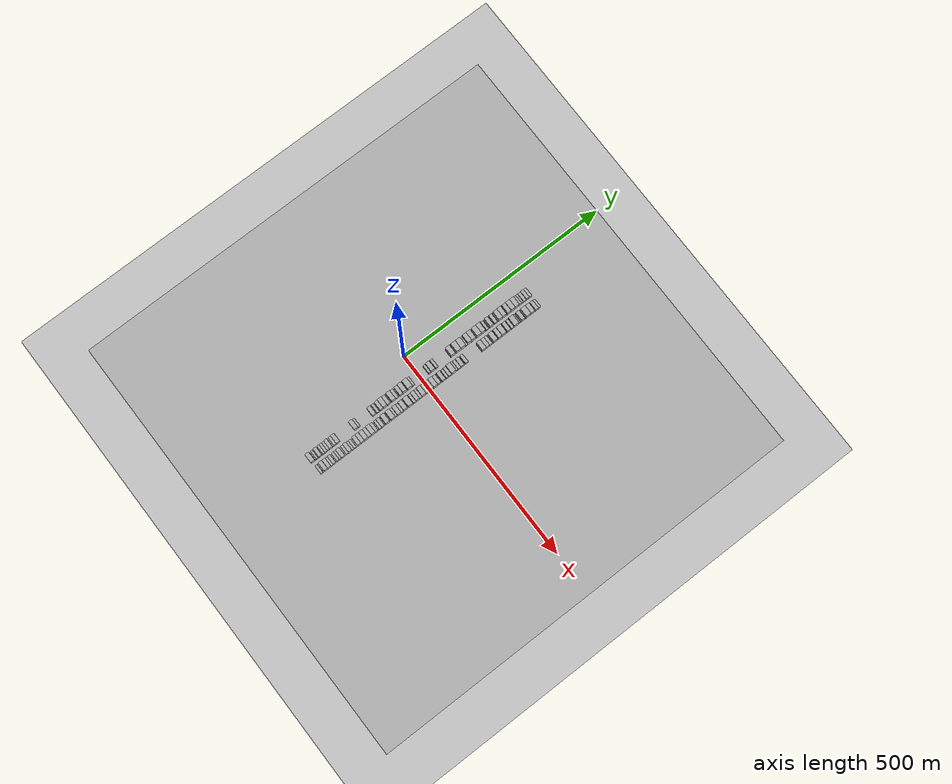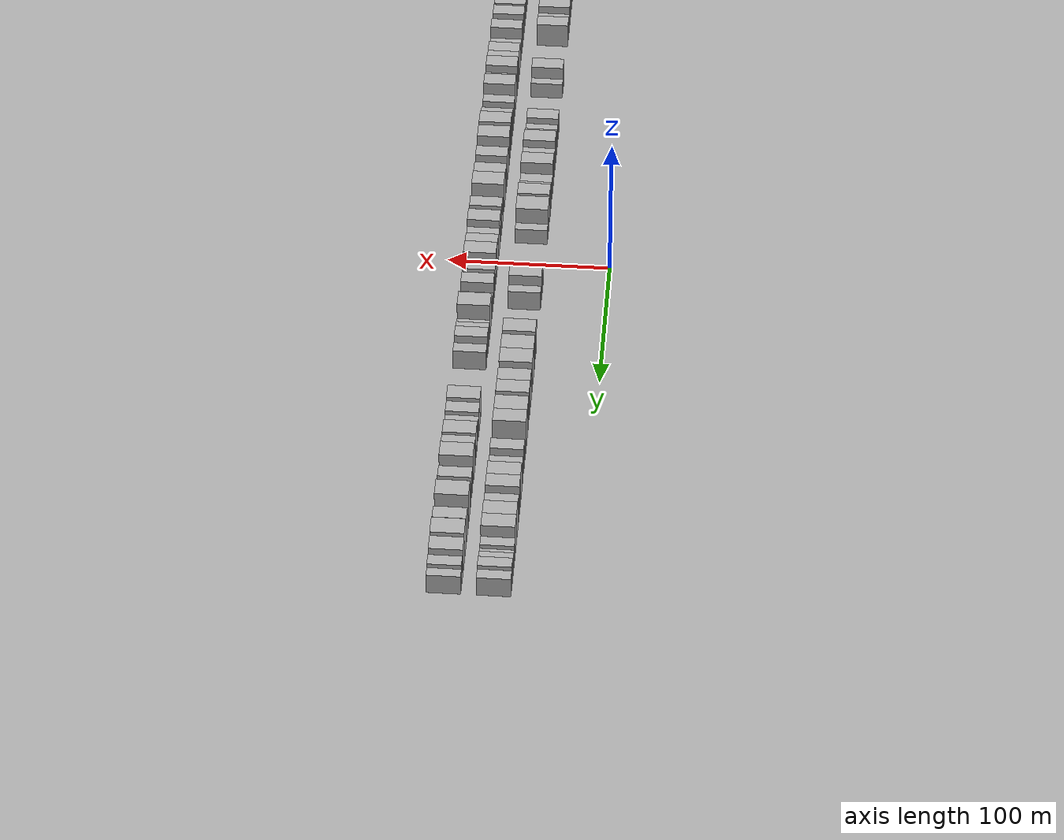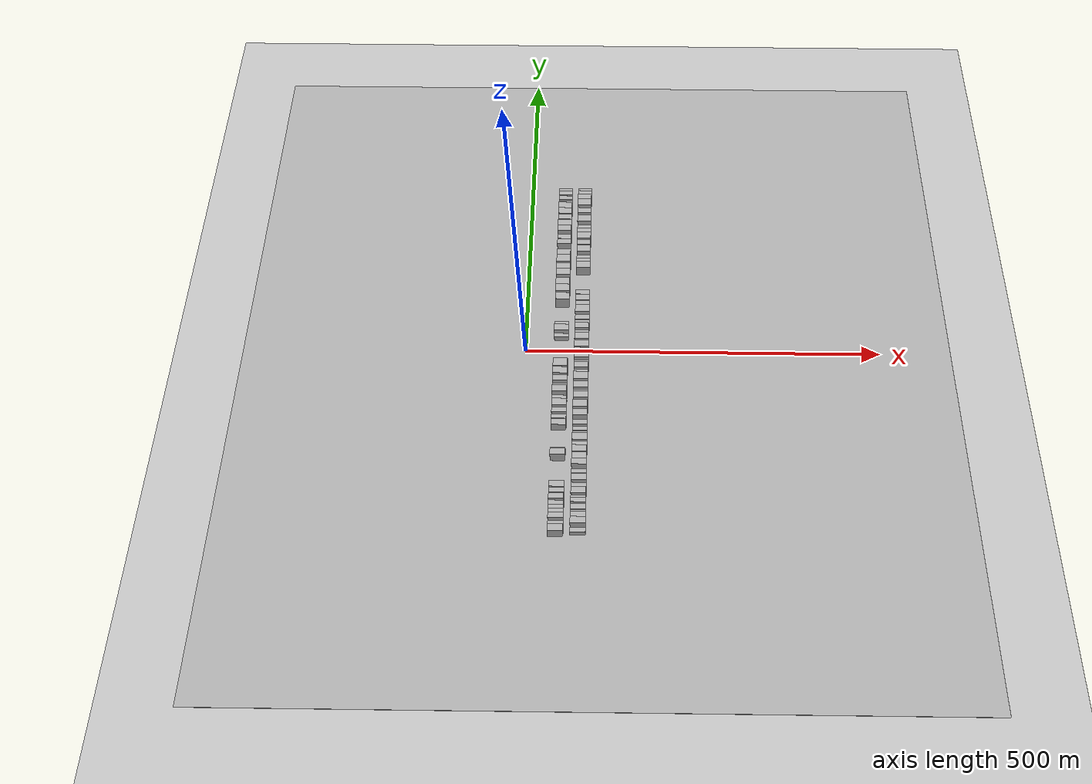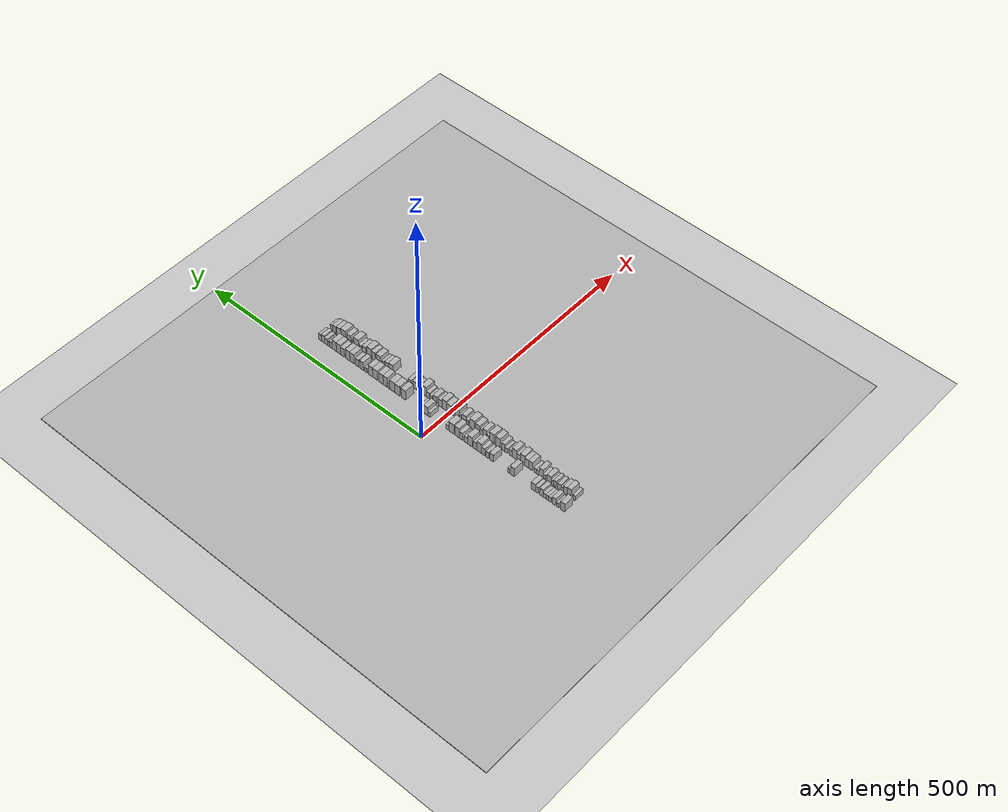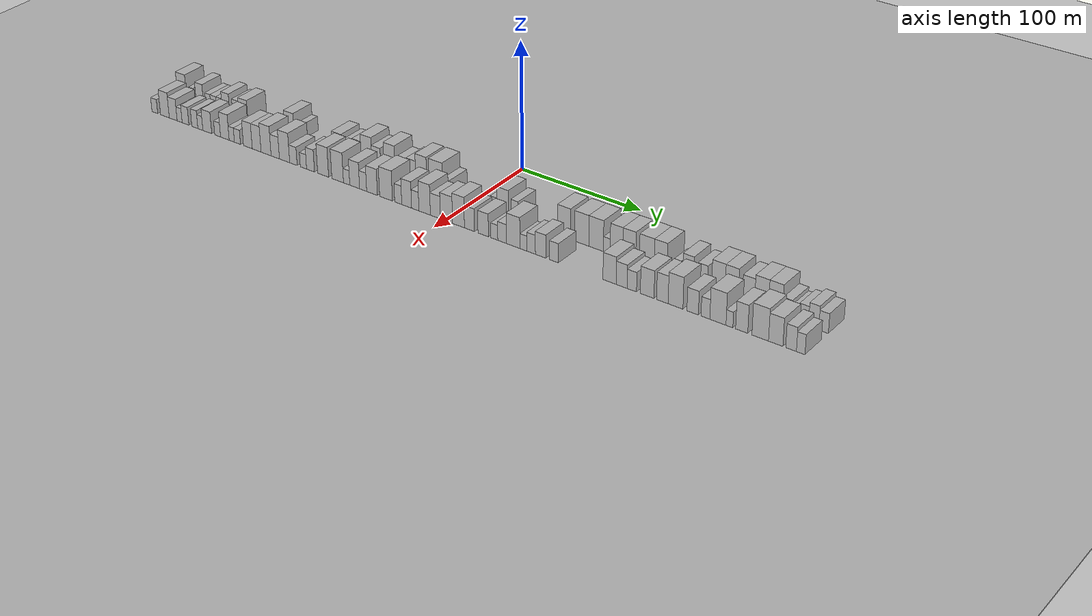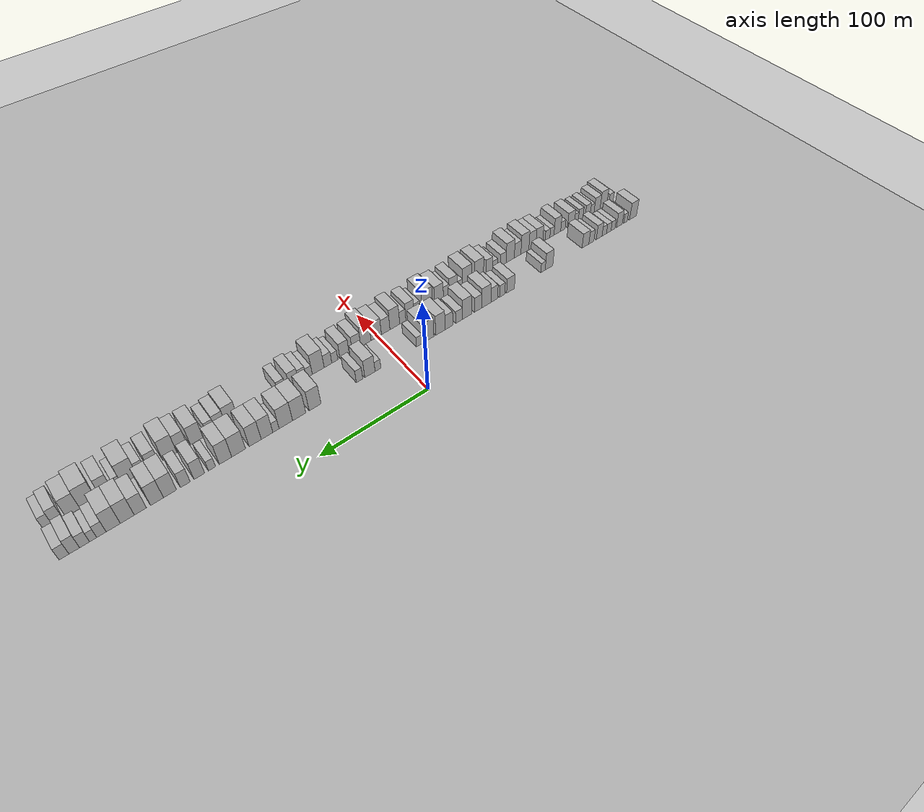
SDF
<?xml version="1.0" encoding="utf-8"?>

<sdf version="1.6">

   <world name="default">

      <gui fullscreen="0">

         <camera name="user_camera">

            <pose>-15 0 4.57585 0 0 0</pose>

            <view_controller>orbit</view_controller>

         </camera>

      </gui>

      <scene>

         <sky>

           <clouds>

             <speed>12</speed>

           </clouds>

         </sky>

         <ambient>0.4 0.4 0.4 1</ambient>

         <background>0.7 0.7 0.7 1</background>

         <shadows>1</shadows>

      </scene>

      <gravity>0 0 -9.8066</gravity>

      <magnetic_field>6e-06 2.3e-05 -4.2e-05</magnetic_field>

      <physics default="0" name="default_physics" type="ode">

         <ode>

            <solver>

               <type>quick</type>

               <iters>10</iters>

               <sor>1.0</sor>

               <use_dynamic_moi_rescaling>0</use_dynamic_moi_rescaling>

            </solver>

            <constraints>

               <cfm>0</cfm>

               <erp>0.2</erp>

               <contact_max_correcting_vel>100</contact_max_correcting_vel>

               <contact_surface_layer>0.001</contact_surface_layer>

            </constraints>

         </ode>

         <max_step_size>0.004</max_step_size>

         <real_time_factor>1</real_time_factor>

         <real_time_update_rate>250</real_time_update_rate>

      </physics>

      <light name="sun" type="directional">

         <cast_shadows>1</cast_shadows>

         <pose>0 0 10 0 0 0</pose>

         <diffuse>0.8 0.8 0.8 1</diffuse>

         <specular>0.2 0.2 0.2 1</specular>

         <attenuation>

            <range>1000</range>

            <constant>0.9</constant>

            <linear>0.01</linear>

            <quadratic>0.001</quadratic>

         </attenuation>

         <direction>-0.5 0.1 -0.9</direction>

      </light>

      <include>

         <name>ground_plane_1</name>

         <uri>model://HANNAS_ground_plane</uri>

         <pose>0 0 0  0 0 0</pose>

      </include>

      <include>

         <name>ground_plane_2</name>

         <uri>model://HANNAS_ground_plane</uri>

         <pose>100 0 0  0 0 0</pose>

      </include>

      <model name="building_1">

         <static>1</static>

         <pose frame="">50.0000 -273.2894 0 0.000000 0.000000 0.000000</pose>

         <link name="link">

            <pose frame="">0 0 10.50 0 0 0</pose>

            <collision name="collision">

               <geometry>

                  <box>

                     <size>20.0000 9.4211 21.0000</size>

                  </box>

               </geometry>

               <max_contacts>10</max_contacts>

               <surface>

                  <contact>

                     <ode/>

                  </contact>

                  <bounce/>

                  <friction>

                     <torsional>

                        <ode/>

                     </torsional>

                     <ode/>

                  </friction>

               </surface>

            </collision>

            <visual name="visual">

               <cast_shadows>0</cast_shadows>

               <geometry>

                  <box>

                     <size>20.0000 9.4211 21.0000</size>

                  </box>

               </geometry>

               <material>

                  <script>

                     <uri>model://HANNAS_wall/materials/scripts</uri>

                     <uri>model://HANNAS_wall/materials/textures</uri>

                     <name>vrc/HANNAS_wall</name>

                  </script>

               </material>

            </visual>

            <self_collide>0</self_collide>

            <enable_wind>0</enable_wind>

            <kinematic>0</kinematic>

         </link>

      </model>

      <model name="building_2">

         <static>1</static>

         <pose frame="">50.0000 -263.1731 0 0.000000 0.000000 0.000000</pose>

         <link name="link">

            <pose frame="">0 0 6.00 0 0 0</pose>

            <collision name="collision">

               <geometry>

                  <box>

                     <size>20.0000 4.8114 12.0000</size>

                  </box>

               </geometry>

               <max_contacts>10</max_contacts>

               <surface>

                  <contact>

                     <ode/>

                  </contact>

                  <bounce/>

                  <friction>

                     <torsional>

                        <ode/>

                     </torsional>

                     <ode/>

                  </friction>

               </surface>

            </collision>

            <visual name="visual">

               <cast_shadows>0</cast_shadows>

               <geometry>

                  <box>

                     <size>20.0000 4.8114 12.0000</size>

                  </box>

               </geometry>

               <material>

                  <script>

                     <uri>model://HANNAS_wall/materials/scripts</uri>

                     <uri>model://HANNAS_wall/materials/textures</uri>

                     <name>vrc/HANNAS_wall</name>

                  </script>

               </material>

            </visual>

            <self_collide>0</self_collide>

            <enable_wind>0</enable_wind>

            <kinematic>0</kinematic>

         </link>

      </model>

      <model name="building_3">

         <static>1</static>

         <pose frame="">50.0000 -254.9956 0 0.000000 0.000000 0.000000</pose>

         <link name="link">

            <pose frame="">0 0 9.00 0 0 0</pose>

            <collision name="collision">

               <geometry>

                  <box>

                     <size>20.0000 7.5438 18.0000</size>

                  </box>

               </geometry>

               <max_contacts>10</max_contacts>

               <surface>

                  <contact>

                     <ode/>

                  </contact>

                  <bounce/>

                  <friction>

                     <torsional>

                        <ode/>

                     </torsional>

                     <ode/>

                  </friction>

               </surface>

            </collision>

            <visual name="visual">

               <cast_shadows>0</cast_shadows>

               <geometry>

                  <box>

                     <size>20.0000 7.5438 18.0000</size>

                  </box>

               </geometry>

               <material>

                  <script>

                     <uri>model://HANNAS_wall/materials/scripts</uri>

                     <uri>model://HANNAS_wall/materials/textures</uri>

                     <name>vrc/HANNAS_wall</name>

                  </script>

               </material>

            </visual>

            <self_collide>0</self_collide>

            <enable_wind>0</enable_wind>

            <kinematic>0</kinematic>

         </link>

      </model>

      <model name="building_4">

         <static>1</static>

         <pose frame="">50.0000 -246.5318 0 0.000000 0.000000 0.000000</pose>

         <link name="link">

            <pose frame="">0 0 6.00 0 0 0</pose>

            <collision name="collision">

               <geometry>

                  <box>

                     <size>20.0000 5.3838 12.0000</size>

                  </box>

               </geometry>

               <max_contacts>10</max_contacts>

               <surface>

                  <contact>

                     <ode/>

                  </contact>

                  <bounce/>

                  <friction>

                     <torsional>

                        <ode/>

                     </torsional>

                     <ode/>

                  </friction>

               </surface>

            </collision>

            <visual name="visual">

               <cast_shadows>0</cast_shadows>

               <geometry>

                  <box>

                     <size>20.0000 5.3838 12.0000</size>

                  </box>

               </geometry>

               <material>

                  <script>

                     <uri>model://HANNAS_wall/materials/scripts</uri>

                     <uri>model://HANNAS_wall/materials/textures</uri>

                     <name>vrc/HANNAS_wall</name>

                  </script>

               </material>

            </visual>

            <self_collide>0</self_collide>

            <enable_wind>0</enable_wind>

            <kinematic>0</kinematic>

         </link>

      </model>

      <model name="building_5">

         <static>1</static>

         <pose frame="">50.0000 -240.9137 0 0.000000 0.000000 0.000000</pose>

         <link name="link">

            <pose frame="">0 0 6.00 0 0 0</pose>

            <collision name="collision">

               <geometry>

                  <box>

                     <size>20.0000 5.8524 12.0000</size>

                  </box>

               </geometry>

               <max_contacts>10</max_contacts>

               <surface>

                  <contact>

                     <ode/>

                  </contact>

                  <bounce/>

                  <friction>

                     <torsional>

                        <ode/>

                     </torsional>

                     <ode/>

                  </friction>

               </surface>

            </collision>

            <visual name="visual">

               <cast_shadows>0</cast_shadows>

               <geometry>

                  <box>

                     <size>20.0000 5.8524 12.0000</size>

                  </box>

               </geometry>

               <material>

                  <script>

                     <uri>model://HANNAS_wall/materials/scripts</uri>

                     <uri>model://HANNAS_wall/materials/textures</uri>

                     <name>vrc/HANNAS_wall</name>

                  </script>

               </material>

            </visual>

            <self_collide>0</self_collide>

            <enable_wind>0</enable_wind>

            <kinematic>0</kinematic>

         </link>

      </model>

      <model name="building_6">

         <static>1</static>

         <pose frame="">50.0000 -235.0717 0 0.000000 0.000000 0.000000</pose>

         <link name="link">

            <pose frame="">0 0 6.00 0 0 0</pose>

            <collision name="collision">

               <geometry>

                  <box>

                     <size>20.0000 5.8316 12.0000</size>

                  </box>

               </geometry>

               <max_contacts>10</max_contacts>

               <surface>

                  <contact>

                     <ode/>

                  </contact>

                  <bounce/>

                  <friction>

                     <torsional>

                        <ode/>

                     </torsional>

                     <ode/>

                  </friction>

               </surface>

            </collision>

            <visual name="visual">

               <cast_shadows>0</cast_shadows>

               <geometry>

                  <box>

                     <size>20.0000 5.8316 12.0000</size>

                  </box>

               </geometry>

               <material>

                  <script>

                     <uri>model://HANNAS_wall/materials/scripts</uri>

                     <uri>model://HANNAS_wall/materials/textures</uri>

                     <name>vrc/HANNAS_wall</name>

                  </script>

               </material>

            </visual>

            <self_collide>0</self_collide>

            <enable_wind>0</enable_wind>

            <kinematic>0</kinematic>

         </link>

      </model>

      <model name="building_7">

         <static>1</static>

         <pose frame="">50.0000 -228.4063 0 0.000000 0.000000 0.000000</pose>

         <link name="link">

            <pose frame="">0 0 9.00 0 0 0</pose>

            <collision name="collision">

               <geometry>

                  <box>

                     <size>20.0000 7.4994 18.0000</size>

                  </box>

               </geometry>

               <max_contacts>10</max_contacts>

               <surface>

                  <contact>

                     <ode/>

                  </contact>

                  <bounce/>

                  <friction>

                     <torsional>

                        <ode/>

                     </torsional>

                     <ode/>

                  </friction>

               </surface>

            </collision>

            <visual name="visual">

               <cast_shadows>0</cast_shadows>

               <geometry>

                  <box>

                     <size>20.0000 7.4994 18.0000</size>

                  </box>

               </geometry>

               <material>

                  <script>

                     <uri>model://HANNAS_wall/materials/scripts</uri>

                     <uri>model://HANNAS_wall/materials/textures</uri>

                     <name>vrc/HANNAS_wall</name>

                  </script>

               </material>

            </visual>

            <self_collide>0</self_collide>

            <enable_wind>0</enable_wind>

            <kinematic>0</kinematic>

         </link>

      </model>

      <model name="building_8">

         <static>1</static>

         <pose frame="">50.0000 -218.4468 0 0.000000 0.000000 0.000000</pose>

         <link name="link">

            <pose frame="">0 0 7.50 0 0 0</pose>

            <collision name="collision">

               <geometry>

                  <box>

                     <size>20.0000 6.4194 15.0000</size>

                  </box>

               </geometry>

               <max_contacts>10</max_contacts>

               <surface>

                  <contact>

                     <ode/>

                  </contact>

                  <bounce/>

                  <friction>

                     <torsional>

                        <ode/>

                     </torsional>

                     <ode/>

                  </friction>

               </surface>

            </collision>

            <visual name="visual">

               <cast_shadows>0</cast_shadows>

               <geometry>

                  <box>

                     <size>20.0000 6.4194 15.0000</size>

                  </box>

               </geometry>

               <material>

                  <script>

                     <uri>model://HANNAS_wall/materials/scripts</uri>

                     <uri>model://HANNAS_wall/materials/textures</uri>

                     <name>vrc/HANNAS_wall</name>

                  </script>

               </material>

            </visual>

            <self_collide>0</self_collide>

            <enable_wind>0</enable_wind>

            <kinematic>0</kinematic>

         </link>

      </model>

      <model name="building_9">

         <static>1</static>

         <pose frame="">50.0000 -210.8716 0 0.000000 0.000000 0.000000</pose>

         <link name="link">

            <pose frame="">0 0 9.00 0 0 0</pose>

            <collision name="collision">

               <geometry>

                  <box>

                     <size>20.0000 8.7310 18.0000</size>

                  </box>

               </geometry>

               <max_contacts>10</max_contacts>

               <surface>

                  <contact>

                     <ode/>

                  </contact>

                  <bounce/>

                  <friction>

                     <torsional>

                        <ode/>

                     </torsional>

                     <ode/>

                  </friction>

               </surface>

            </collision>

            <visual name="visual">

               <cast_shadows>0</cast_shadows>

               <geometry>

                  <box>

                     <size>20.0000 8.7310 18.0000</size>

                  </box>

               </geometry>

               <material>

                  <script>

                     <uri>model://HANNAS_wall/materials/scripts</uri>

                     <uri>model://HANNAS_wall/materials/textures</uri>

                     <name>vrc/HANNAS_wall</name>

                  </script>

               </material>

            </visual>

            <self_collide>0</self_collide>

            <enable_wind>0</enable_wind>

            <kinematic>0</kinematic>

         </link>

      </model>

      <model name="building_10">

         <static>1</static>

         <pose frame="">50.0000 -165.6635 0 0.000000 0.000000 0.000000</pose>

         <link name="link">

            <pose frame="">0 0 10.50 0 0 0</pose>

            <collision name="collision">

               <geometry>

                  <box>

                     <size>20.0000 9.2284 21.0000</size>

                  </box>

               </geometry>

               <max_contacts>10</max_contacts>

               <surface>

                  <contact>

                     <ode/>

                  </contact>

                  <bounce/>

                  <friction>

                     <torsional>

                        <ode/>

                     </torsional>

                     <ode/>

                  </friction>

               </surface>

            </collision>

            <visual name="visual">

               <cast_shadows>0</cast_shadows>

               <geometry>

                  <box>

                     <size>20.0000 9.2284 21.0000</size>

                  </box>

               </geometry>

               <material>

                  <script>

                     <uri>model://HANNAS_wall/materials/scripts</uri>

                     <uri>model://HANNAS_wall/materials/textures</uri>

                     <name>vrc/HANNAS_wall</name>

                  </script>

               </material>

            </visual>

            <self_collide>0</self_collide>

            <enable_wind>0</enable_wind>

            <kinematic>0</kinematic>

         </link>

      </model>

      <model name="building_11">

         <static>1</static>

         <pose frame="">50.0000 -158.4213 0 0.000000 0.000000 0.000000</pose>

         <link name="link">

            <pose frame="">0 0 6.00 0 0 0</pose>

            <collision name="collision">

               <geometry>

                  <box>

                     <size>20.0000 5.2560 12.0000</size>

                  </box>

               </geometry>

               <max_contacts>10</max_contacts>

               <surface>

                  <contact>

                     <ode/>

                  </contact>

                  <bounce/>

                  <friction>

                     <torsional>

                        <ode/>

                     </torsional>

                     <ode/>

                  </friction>

               </surface>

            </collision>

            <visual name="visual">

               <cast_shadows>0</cast_shadows>

               <geometry>

                  <box>

                     <size>20.0000 5.2560 12.0000</size>

                  </box>

               </geometry>

               <material>

                  <script>

                     <uri>model://HANNAS_wall/materials/scripts</uri>

                     <uri>model://HANNAS_wall/materials/textures</uri>

                     <name>vrc/HANNAS_wall</name>

                  </script>

               </material>

            </visual>

            <self_collide>0</self_collide>

            <enable_wind>0</enable_wind>

            <kinematic>0</kinematic>

         </link>

      </model>

      <model name="building_12">

         <static>1</static>

         <pose frame="">50.0000 -120.2953 0 0.000000 0.000000 0.000000</pose>

         <link name="link">

            <pose frame="">0 0 9.00 0 0 0</pose>

            <collision name="collision">

               <geometry>

                  <box>

                     <size>20.0000 8.9987 18.0000</size>

                  </box>

               </geometry>

               <max_contacts>10</max_contacts>

               <surface>

                  <contact>

                     <ode/>

                  </contact>

                  <bounce/>

                  <friction>

                     <torsional>

                        <ode/>

                     </torsional>

                     <ode/>

                  </friction>

               </surface>

            </collision>

            <visual name="visual">

               <cast_shadows>0</cast_shadows>

               <geometry>

                  <box>

                     <size>20.0000 8.9987 18.0000</size>

                  </box>

               </geometry>

               <material>

                  <script>

                     <uri>model://HANNAS_wall/materials/scripts</uri>

                     <uri>model://HANNAS_wall/materials/textures</uri>

                     <name>vrc/HANNAS_wall</name>

                  </script>

               </material>

            </visual>

            <self_collide>0</self_collide>

            <enable_wind>0</enable_wind>

            <kinematic>0</kinematic>

         </link>

      </model>

      <model name="building_13">

         <static>1</static>

         <pose frame="">50.0000 -110.7217 0 0.000000 0.000000 0.000000</pose>

         <link name="link">

            <pose frame="">0 0 7.50 0 0 0</pose>

            <collision name="collision">

               <geometry>

                  <box>

                     <size>20.0000 6.1485 15.0000</size>

                  </box>

               </geometry>

               <max_contacts>10</max_contacts>

               <surface>

                  <contact>

                     <ode/>

                  </contact>

                  <bounce/>

                  <friction>

                     <torsional>

                        <ode/>

                     </torsional>

                     <ode/>

                  </friction>

               </surface>

            </collision>

            <visual name="visual">

               <cast_shadows>0</cast_shadows>

               <geometry>

                  <box>

                     <size>20.0000 6.1485 15.0000</size>

                  </box>

               </geometry>

               <material>

                  <script>

                     <uri>model://HANNAS_wall/materials/scripts</uri>

                     <uri>model://HANNAS_wall/materials/textures</uri>

                     <name>vrc/HANNAS_wall</name>

                  </script>

               </material>

            </visual>

            <self_collide>0</self_collide>

            <enable_wind>0</enable_wind>

            <kinematic>0</kinematic>

         </link>

      </model>

      <model name="building_14">

         <static>1</static>

         <pose frame="">50.0000 -101.7950 0 0.000000 0.000000 0.000000</pose>

         <link name="link">

            <pose frame="">0 0 9.00 0 0 0</pose>

            <collision name="collision">

               <geometry>

                  <box>

                     <size>20.0000 7.7049 18.0000</size>

                  </box>

               </geometry>

               <max_contacts>10</max_contacts>

               <surface>

                  <contact>

                     <ode/>

                  </contact>

                  <bounce/>

                  <friction>

                     <torsional>

                        <ode/>

                     </torsional>

                     <ode/>

                  </friction>

               </surface>

            </collision>

            <visual name="visual">

               <cast_shadows>0</cast_shadows>

               <geometry>

                  <box>

                     <size>20.0000 7.7049 18.0000</size>

                  </box>

               </geometry>

               <material>

                  <script>

                     <uri>model://HANNAS_wall/materials/scripts</uri>

                     <uri>model://HANNAS_wall/materials/textures</uri>

                     <name>vrc/HANNAS_wall</name>

                  </script>

               </material>

            </visual>

            <self_collide>0</self_collide>

            <enable_wind>0</enable_wind>

            <kinematic>0</kinematic>

         </link>

      </model>

      <model name="building_15">

         <static>1</static>

         <pose frame="">50.0000 -92.9218 0 0.000000 0.000000 0.000000</pose>

         <link name="link">

            <pose frame="">0 0 12.00 0 0 0</pose>

            <collision name="collision">

               <geometry>

                  <box>

                     <size>20.0000 10.0415 24.0000</size>

                  </box>

               </geometry>

               <max_contacts>10</max_contacts>

               <surface>

                  <contact>

                     <ode/>

                  </contact>

                  <bounce/>

                  <friction>

                     <torsional>

                        <ode/>

                     </torsional>

                     <ode/>

                  </friction>

               </surface>

            </collision>

            <visual name="visual">

               <cast_shadows>0</cast_shadows>

               <geometry>

                  <box>

                     <size>20.0000 10.0415 24.0000</size>

                  </box>

               </geometry>

               <material>

                  <script>

                     <uri>model://HANNAS_wall/materials/scripts</uri>

                     <uri>model://HANNAS_wall/materials/textures</uri>

                     <name>vrc/HANNAS_wall</name>

                  </script>

               </material>

            </visual>

            <self_collide>0</self_collide>

            <enable_wind>0</enable_wind>

            <kinematic>0</kinematic>

         </link>

      </model>

      <model name="building_16">

         <static>1</static>

         <pose frame="">50.0000 -83.8574 0 0.000000 0.000000 0.000000</pose>

         <link name="link">

            <pose frame="">0 0 9.00 0 0 0</pose>

            <collision name="collision">

               <geometry>

                  <box>

                     <size>20.0000 8.0873 18.0000</size>

                  </box>

               </geometry>

               <max_contacts>10</max_contacts>

               <surface>

                  <contact>

                     <ode/>

                  </contact>

                  <bounce/>

                  <friction>

                     <torsional>

                        <ode/>

                     </torsional>

                     <ode/>

                  </friction>

               </surface>

            </collision>

            <visual name="visual">

               <cast_shadows>0</cast_shadows>

               <geometry>

                  <box>

                     <size>20.0000 8.0873 18.0000</size>

                  </box>

               </geometry>

               <material>

                  <script>

                     <uri>model://HANNAS_wall/materials/scripts</uri>

                     <uri>model://HANNAS_wall/materials/textures</uri>

                     <name>vrc/HANNAS_wall</name>

                  </script>

               </material>

            </visual>

            <self_collide>0</self_collide>

            <enable_wind>0</enable_wind>

            <kinematic>0</kinematic>

         </link>

      </model>

      <model name="building_17">

         <static>1</static>

         <pose frame="">50.0000 -71.8088 0 0.000000 0.000000 0.000000</pose>

         <link name="link">

            <pose frame="">0 0 12.00 0 0 0</pose>

            <collision name="collision">

               <geometry>

                  <box>

                     <size>20.0000 10.0099 24.0000</size>

                  </box>

               </geometry>

               <max_contacts>10</max_contacts>

               <surface>

                  <contact>

                     <ode/>

                  </contact>

                  <bounce/>

                  <friction>

                     <torsional>

                        <ode/>

                     </torsional>

                     <ode/>

                  </friction>

               </surface>

            </collision>

            <visual name="visual">

               <cast_shadows>0</cast_shadows>

               <geometry>

                  <box>

                     <size>20.0000 10.0099 24.0000</size>

                  </box>

               </geometry>

               <material>

                  <script>

                     <uri>model://HANNAS_wall/materials/scripts</uri>

                     <uri>model://HANNAS_wall/materials/textures</uri>

                     <name>vrc/HANNAS_wall</name>

                  </script>

               </material>

            </visual>

            <self_collide>0</self_collide>

            <enable_wind>0</enable_wind>

            <kinematic>0</kinematic>

         </link>

      </model>

      <model name="building_18">

         <static>1</static>

         <pose frame="">50.0000 -63.0644 0 0.000000 0.000000 0.000000</pose>

         <link name="link">

            <pose frame="">0 0 7.50 0 0 0</pose>

            <collision name="collision">

               <geometry>

                  <box>

                     <size>20.0000 7.4788 15.0000</size>

                  </box>

               </geometry>

               <max_contacts>10</max_contacts>

               <surface>

                  <contact>

                     <ode/>

                  </contact>

                  <bounce/>

                  <friction>

                     <torsional>

                        <ode/>

                     </torsional>

                     <ode/>

                  </friction>

               </surface>

            </collision>

            <visual name="visual">

               <cast_shadows>0</cast_shadows>

               <geometry>

                  <box>

                     <size>20.0000 7.4788 15.0000</size>

                  </box>

               </geometry>

               <material>

                  <script>

                     <uri>model://HANNAS_wall/materials/scripts</uri>

                     <uri>model://HANNAS_wall/materials/textures</uri>

                     <name>vrc/HANNAS_wall</name>

                  </script>

               </material>

            </visual>

            <self_collide>0</self_collide>

            <enable_wind>0</enable_wind>

            <kinematic>0</kinematic>

         </link>

      </model>

      <model name="building_19">

         <static>1</static>

         <pose frame="">50.0000 -52.2346 0 0.000000 0.000000 0.000000</pose>

         <link name="link">

            <pose frame="">0 0 9.00 0 0 0</pose>

            <collision name="collision">

               <geometry>

                  <box>

                     <size>20.0000 8.1807 18.0000</size>

                  </box>

               </geometry>

               <max_contacts>10</max_contacts>

               <surface>

                  <contact>

                     <ode/>

                  </contact>

                  <bounce/>

                  <friction>

                     <torsional>

                        <ode/>

                     </torsional>

                     <ode/>

                  </friction>

               </surface>

            </collision>

            <visual name="visual">

               <cast_shadows>0</cast_shadows>

               <geometry>

                  <box>

                     <size>20.0000 8.1807 18.0000</size>

                  </box>

               </geometry>

               <material>

                  <script>

                     <uri>model://HANNAS_wall/materials/scripts</uri>

                     <uri>model://HANNAS_wall/materials/textures</uri>

                     <name>vrc/HANNAS_wall</name>

                  </script>

               </material>

            </visual>

            <self_collide>0</self_collide>

            <enable_wind>0</enable_wind>

            <kinematic>0</kinematic>

         </link>

      </model>

      <model name="building_20">

         <static>1</static>

         <pose frame="">50.0000 -43.2268 0 0.000000 0.000000 0.000000</pose>

         <link name="link">

            <pose frame="">0 0 12.00 0 0 0</pose>

            <collision name="collision">

               <geometry>

                  <box>

                     <size>20.0000 9.8349 24.0000</size>

                  </box>

               </geometry>

               <max_contacts>10</max_contacts>

               <surface>

                  <contact>

                     <ode/>

                  </contact>

                  <bounce/>

                  <friction>

                     <torsional>

                        <ode/>

                     </torsional>

                     <ode/>

                  </friction>

               </surface>

            </collision>

            <visual name="visual">

               <cast_shadows>0</cast_shadows>

               <geometry>

                  <box>

                     <size>20.0000 9.8349 24.0000</size>

                  </box>

               </geometry>

               <material>

                  <script>

                     <uri>model://HANNAS_wall/materials/scripts</uri>

                     <uri>model://HANNAS_wall/materials/textures</uri>

                     <name>vrc/HANNAS_wall</name>

                  </script>

               </material>

            </visual>

            <self_collide>0</self_collide>

            <enable_wind>0</enable_wind>

            <kinematic>0</kinematic>

         </link>

      </model>

      <model name="building_21">

         <static>1</static>

         <pose frame="">50.0000 -30.3113 0 0.000000 0.000000 0.000000</pose>

         <link name="link">

            <pose frame="">0 0 12.00 0 0 0</pose>

            <collision name="collision">

               <geometry>

                  <box>

                     <size>20.0000 11.9960 24.0000</size>

                  </box>

               </geometry>

               <max_contacts>10</max_contacts>

               <surface>

                  <contact>

                     <ode/>

                  </contact>

                  <bounce/>

                  <friction>

                     <torsional>

                        <ode/>

                     </torsional>

                     <ode/>

                  </friction>

               </surface>

            </collision>

            <visual name="visual">

               <cast_shadows>0</cast_shadows>

               <geometry>

                  <box>

                     <size>20.0000 11.9960 24.0000</size>

                  </box>

               </geometry>

               <material>

                  <script>

                     <uri>model://HANNAS_wall/materials/scripts</uri>

                     <uri>model://HANNAS_wall/materials/textures</uri>

                     <name>vrc/HANNAS_wall</name>

                  </script>

               </material>

            </visual>

            <self_collide>0</self_collide>

            <enable_wind>0</enable_wind>

            <kinematic>0</kinematic>

         </link>

      </model>

      <model name="building_22">

         <static>1</static>

         <pose frame="">50.0000 -21.3489 0 0.000000 0.000000 0.000000</pose>

         <link name="link">

            <pose frame="">0 0 6.00 0 0 0</pose>

            <collision name="collision">

               <geometry>

                  <box>

                     <size>20.0000 5.9289 12.0000</size>

                  </box>

               </geometry>

               <max_contacts>10</max_contacts>

               <surface>

                  <contact>

                     <ode/>

                  </contact>

                  <bounce/>

                  <friction>

                     <torsional>

                        <ode/>

                     </torsional>

                     <ode/>

                  </friction>

               </surface>

            </collision>

            <visual name="visual">

               <cast_shadows>0</cast_shadows>

               <geometry>

                  <box>

                     <size>20.0000 5.9289 12.0000</size>

                  </box>

               </geometry>

               <material>

                  <script>

                     <uri>model://HANNAS_wall/materials/scripts</uri>

                     <uri>model://HANNAS_wall/materials/textures</uri>

                     <name>vrc/HANNAS_wall</name>

                  </script>

               </material>

            </visual>

            <self_collide>0</self_collide>

            <enable_wind>0</enable_wind>

            <kinematic>0</kinematic>

         </link>

      </model>

      <model name="building_23">

         <static>1</static>

         <pose frame="">50.0000 20.0365 0 0.000000 0.000000 0.000000</pose>

         <link name="link">

            <pose frame="">0 0 6.00 0 0 0</pose>

            <collision name="collision">

               <geometry>

                  <box>

                     <size>20.0000 5.6139 12.0000</size>

                  </box>

               </geometry>

               <max_contacts>10</max_contacts>

               <surface>

                  <contact>

                     <ode/>

                  </contact>

                  <bounce/>

                  <friction>

                     <torsional>

                        <ode/>

                     </torsional>

                     <ode/>

                  </friction>

               </surface>

            </collision>

            <visual name="visual">

               <cast_shadows>0</cast_shadows>

               <geometry>

                  <box>

                     <size>20.0000 5.6139 12.0000</size>

                  </box>

               </geometry>

               <material>

                  <script>

                     <uri>model://HANNAS_wall/materials/scripts</uri>

                     <uri>model://HANNAS_wall/materials/textures</uri>

                     <name>vrc/HANNAS_wall</name>

                  </script>

               </material>

            </visual>

            <self_collide>0</self_collide>

            <enable_wind>0</enable_wind>

            <kinematic>0</kinematic>

         </link>

      </model>

      <model name="building_24">

         <static>1</static>

         <pose frame="">50.0000 27.7827 0 0.000000 0.000000 0.000000</pose>

         <link name="link">

            <pose frame="">0 0 10.50 0 0 0</pose>

            <collision name="collision">

               <geometry>

                  <box>

                     <size>20.0000 9.8785 21.0000</size>

                  </box>

               </geometry>

               <max_contacts>10</max_contacts>

               <surface>

                  <contact>

                     <ode/>

                  </contact>

                  <bounce/>

                  <friction>

                     <torsional>

                        <ode/>

                     </torsional>

                     <ode/>

                  </friction>

               </surface>

            </collision>

            <visual name="visual">

               <cast_shadows>0</cast_shadows>

               <geometry>

                  <box>

                     <size>20.0000 9.8785 21.0000</size>

                  </box>

               </geometry>

               <material>

                  <script>

                     <uri>model://HANNAS_wall/materials/scripts</uri>

                     <uri>model://HANNAS_wall/materials/textures</uri>

                     <name>vrc/HANNAS_wall</name>

                  </script>

               </material>

            </visual>

            <self_collide>0</self_collide>

            <enable_wind>0</enable_wind>

            <kinematic>0</kinematic>

         </link>

      </model>

      <model name="building_25">

         <static>1</static>

         <pose frame="">50.0000 37.7864 0 0.000000 0.000000 0.000000</pose>

         <link name="link">

            <pose frame="">0 0 7.50 0 0 0</pose>

            <collision name="collision">

               <geometry>

                  <box>

                     <size>20.0000 6.1289 15.0000</size>

                  </box>

               </geometry>

               <max_contacts>10</max_contacts>

               <surface>

                  <contact>

                     <ode/>

                  </contact>

                  <bounce/>

                  <friction>

                     <torsional>

                        <ode/>

                     </torsional>

                     <ode/>

                  </friction>

               </surface>

            </collision>

            <visual name="visual">

               <cast_shadows>0</cast_shadows>

               <geometry>

                  <box>

                     <size>20.0000 6.1289 15.0000</size>

                  </box>

               </geometry>

               <material>

                  <script>

                     <uri>model://HANNAS_wall/materials/scripts</uri>

                     <uri>model://HANNAS_wall/materials/textures</uri>

                     <name>vrc/HANNAS_wall</name>

                  </script>

               </material>

            </visual>

            <self_collide>0</self_collide>

            <enable_wind>0</enable_wind>

            <kinematic>0</kinematic>

         </link>

      </model>

      <model name="building_26">

         <static>1</static>

         <pose frame="">50.0000 79.0097 0 0.000000 0.000000 0.000000</pose>

         <link name="link">

            <pose frame="">0 0 12.00 0 0 0</pose>

            <collision name="collision">

               <geometry>

                  <box>

                     <size>20.0000 10.7726 24.0000</size>

                  </box>

               </geometry>

               <max_contacts>10</max_contacts>

               <surface>

                  <contact>

                     <ode/>

                  </contact>

                  <bounce/>

                  <friction>

                     <torsional>

                        <ode/>

                     </torsional>

                     <ode/>

                  </friction>

               </surface>

            </collision>

            <visual name="visual">

               <cast_shadows>0</cast_shadows>

               <geometry>

                  <box>

                     <size>20.0000 10.7726 24.0000</size>

                  </box>

               </geometry>

               <material>

                  <script>

                     <uri>model://HANNAS_wall/materials/scripts</uri>

                     <uri>model://HANNAS_wall/materials/textures</uri>

                     <name>vrc/HANNAS_wall</name>

                  </script>

               </material>

            </visual>

            <self_collide>0</self_collide>

            <enable_wind>0</enable_wind>

            <kinematic>0</kinematic>

         </link>

      </model>

      <model name="building_27">

         <static>1</static>

         <pose frame="">50.0000 93.2455 0 0.000000 0.000000 0.000000</pose>

         <link name="link">

            <pose frame="">0 0 12.00 0 0 0</pose>

            <collision name="collision">

               <geometry>

                  <box>

                     <size>20.0000 11.6992 24.0000</size>

                  </box>

               </geometry>

               <max_contacts>10</max_contacts>

               <surface>

                  <contact>

                     <ode/>

                  </contact>

                  <bounce/>

                  <friction>

                     <torsional>

                        <ode/>

                     </torsional>

                     <ode/>

                  </friction>

               </surface>

            </collision>

            <visual name="visual">

               <cast_shadows>0</cast_shadows>

               <geometry>

                  <box>

                     <size>20.0000 11.6992 24.0000</size>

                  </box>

               </geometry>

               <material>

                  <script>

                     <uri>model://HANNAS_wall/materials/scripts</uri>

                     <uri>model://HANNAS_wall/materials/textures</uri>

                     <name>vrc/HANNAS_wall</name>

                  </script>

               </material>

            </visual>

            <self_collide>0</self_collide>

            <enable_wind>0</enable_wind>

            <kinematic>0</kinematic>

         </link>

      </model>

      <model name="building_28">

         <static>1</static>

         <pose frame="">50.0000 105.0080 0 0.000000 0.000000 0.000000</pose>

         <link name="link">

            <pose frame="">0 0 12.00 0 0 0</pose>

            <collision name="collision">

               <geometry>

                  <box>

                     <size>20.0000 11.8258 24.0000</size>

                  </box>

               </geometry>

               <max_contacts>10</max_contacts>

               <surface>

                  <contact>

                     <ode/>

                  </contact>

                  <bounce/>

                  <friction>

                     <torsional>

                        <ode/>

                     </torsional>

                     <ode/>

                  </friction>

               </surface>

            </collision>

            <visual name="visual">

               <cast_shadows>0</cast_shadows>

               <geometry>

                  <box>

                     <size>20.0000 11.8258 24.0000</size>

                  </box>

               </geometry>

               <material>

                  <script>

                     <uri>model://HANNAS_wall/materials/scripts</uri>

                     <uri>model://HANNAS_wall/materials/textures</uri>

                     <name>vrc/HANNAS_wall</name>

                  </script>

               </material>

            </visual>

            <self_collide>0</self_collide>

            <enable_wind>0</enable_wind>

            <kinematic>0</kinematic>

         </link>

      </model>

      <model name="building_29">

         <static>1</static>

         <pose frame="">50.0000 113.6295 0 0.000000 0.000000 0.000000</pose>

         <link name="link">

            <pose frame="">0 0 6.00 0 0 0</pose>

            <collision name="collision">

               <geometry>

                  <box>

                     <size>20.0000 5.4173 12.0000</size>

                  </box>

               </geometry>

               <max_contacts>10</max_contacts>

               <surface>

                  <contact>

                     <ode/>

                  </contact>

                  <bounce/>

                  <friction>

                     <torsional>

                        <ode/>

                     </torsional>

                     <ode/>

                  </friction>

               </surface>

            </collision>

            <visual name="visual">

               <cast_shadows>0</cast_shadows>

               <geometry>

                  <box>

                     <size>20.0000 5.4173 12.0000</size>

                  </box>

               </geometry>

               <material>

                  <script>

                     <uri>model://HANNAS_wall/materials/scripts</uri>

                     <uri>model://HANNAS_wall/materials/textures</uri>

                     <name>vrc/HANNAS_wall</name>

                  </script>

               </material>

            </visual>

            <self_collide>0</self_collide>

            <enable_wind>0</enable_wind>

            <kinematic>0</kinematic>

         </link>

      </model>

      <model name="building_30">

         <static>1</static>

         <pose frame="">50.0000 121.3098 0 0.000000 0.000000 0.000000</pose>

         <link name="link">

            <pose frame="">0 0 12.00 0 0 0</pose>

            <collision name="collision">

               <geometry>

                  <box>

                     <size>20.0000 9.9432 24.0000</size>

                  </box>

               </geometry>

               <max_contacts>10</max_contacts>

               <surface>

                  <contact>

                     <ode/>

                  </contact>

                  <bounce/>

                  <friction>

                     <torsional>

                        <ode/>

                     </torsional>

                     <ode/>

                  </friction>

               </surface>

            </collision>

            <visual name="visual">

               <cast_shadows>0</cast_shadows>

               <geometry>

                  <box>

                     <size>20.0000 9.9432 24.0000</size>

                  </box>

               </geometry>

               <material>

                  <script>

                     <uri>model://HANNAS_wall/materials/scripts</uri>

                     <uri>model://HANNAS_wall/materials/textures</uri>

                     <name>vrc/HANNAS_wall</name>

                  </script>

               </material>

            </visual>

            <self_collide>0</self_collide>

            <enable_wind>0</enable_wind>

            <kinematic>0</kinematic>

         </link>

      </model>

      <model name="building_31">

         <static>1</static>

         <pose frame="">50.0000 131.3700 0 0.000000 0.000000 0.000000</pose>

         <link name="link">

            <pose frame="">0 0 12.00 0 0 0</pose>

            <collision name="collision">

               <geometry>

                  <box>

                     <size>20.0000 10.1771 24.0000</size>

                  </box>

               </geometry>

               <max_contacts>10</max_contacts>

               <surface>

                  <contact>

                     <ode/>

                  </contact>

                  <bounce/>

                  <friction>

                     <torsional>

                        <ode/>

                     </torsional>

                     <ode/>

                  </friction>

               </surface>

            </collision>

            <visual name="visual">

               <cast_shadows>0</cast_shadows>

               <geometry>

                  <box>

                     <size>20.0000 10.1771 24.0000</size>

                  </box>

               </geometry>

               <material>

                  <script>

                     <uri>model://HANNAS_wall/materials/scripts</uri>

                     <uri>model://HANNAS_wall/materials/textures</uri>

                     <name>vrc/HANNAS_wall</name>

                  </script>

               </material>

            </visual>

            <self_collide>0</self_collide>

            <enable_wind>0</enable_wind>

            <kinematic>0</kinematic>

         </link>

      </model>

      <model name="building_32">

         <static>1</static>

         <pose frame="">50.0000 145.2231 0 0.000000 0.000000 0.000000</pose>

         <link name="link">

            <pose frame="">0 0 12.00 0 0 0</pose>

            <collision name="collision">

               <geometry>

                  <box>

                     <size>20.0000 11.5292 24.0000</size>

                  </box>

               </geometry>

               <max_contacts>10</max_contacts>

               <surface>

                  <contact>

                     <ode/>

                  </contact>

                  <bounce/>

                  <friction>

                     <torsional>

                        <ode/>

                     </torsional>

                     <ode/>

                  </friction>

               </surface>

            </collision>

            <visual name="visual">

               <cast_shadows>0</cast_shadows>

               <geometry>

                  <box>

                     <size>20.0000 11.5292 24.0000</size>

                  </box>

               </geometry>

               <material>

                  <script>

                     <uri>model://HANNAS_wall/materials/scripts</uri>

                     <uri>model://HANNAS_wall/materials/textures</uri>

                     <name>vrc/HANNAS_wall</name>

                  </script>

               </material>

            </visual>

            <self_collide>0</self_collide>

            <enable_wind>0</enable_wind>

            <kinematic>0</kinematic>

         </link>

      </model>

      <model name="building_33">

         <static>1</static>

         <pose frame="">50.0000 156.0514 0 0.000000 0.000000 0.000000</pose>

         <link name="link">

            <pose frame="">0 0 12.00 0 0 0</pose>

            <collision name="collision">

               <geometry>

                  <box>

                     <size>20.0000 10.1275 24.0000</size>

                  </box>

               </geometry>

               <max_contacts>10</max_contacts>

               <surface>

                  <contact>

                     <ode/>

                  </contact>

                  <bounce/>

                  <friction>

                     <torsional>

                        <ode/>

                     </torsional>

                     <ode/>

                  </friction>

               </surface>

            </collision>

            <visual name="visual">

               <cast_shadows>0</cast_shadows>

               <geometry>

                  <box>

                     <size>20.0000 10.1275 24.0000</size>

                  </box>

               </geometry>

               <material>

                  <script>

                     <uri>model://HANNAS_wall/materials/scripts</uri>

                     <uri>model://HANNAS_wall/materials/textures</uri>

                     <name>vrc/HANNAS_wall</name>

                  </script>

               </material>

            </visual>

            <self_collide>0</self_collide>

            <enable_wind>0</enable_wind>

            <kinematic>0</kinematic>

         </link>

      </model>

      <model name="building_34">

         <static>1</static>

         <pose frame="">50.0000 167.0105 0 0.000000 0.000000 0.000000</pose>

         <link name="link">

            <pose frame="">0 0 6.00 0 0 0</pose>

            <collision name="collision">

               <geometry>

                  <box>

                     <size>20.0000 5.7908 12.0000</size>

                  </box>

               </geometry>

               <max_contacts>10</max_contacts>

               <surface>

                  <contact>

                     <ode/>

                  </contact>

                  <bounce/>

                  <friction>

                     <torsional>

                        <ode/>

                     </torsional>

                     <ode/>

                  </friction>

               </surface>

            </collision>

            <visual name="visual">

               <cast_shadows>0</cast_shadows>

               <geometry>

                  <box>

                     <size>20.0000 5.7908 12.0000</size>

                  </box>

               </geometry>

               <material>

                  <script>

                     <uri>model://HANNAS_wall/materials/scripts</uri>

                     <uri>model://HANNAS_wall/materials/textures</uri>

                     <name>vrc/HANNAS_wall</name>

                  </script>

               </material>

            </visual>

            <self_collide>0</self_collide>

            <enable_wind>0</enable_wind>

            <kinematic>0</kinematic>

         </link>

      </model>

      <model name="building_35">

         <static>1</static>

         <pose frame="">50.0000 177.1326 0 0.000000 0.000000 0.000000</pose>

         <link name="link">

            <pose frame="">0 0 10.50 0 0 0</pose>

            <collision name="collision">

               <geometry>

                  <box>

                     <size>20.0000 8.4533 21.0000</size>

                  </box>

               </geometry>

               <max_contacts>10</max_contacts>

               <surface>

                  <contact>

                     <ode/>

                  </contact>

                  <bounce/>

                  <friction>

                     <torsional>

                        <ode/>

                     </torsional>

                     <ode/>

                  </friction>

               </surface>

            </collision>

            <visual name="visual">

               <cast_shadows>0</cast_shadows>

               <geometry>

                  <box>

                     <size>20.0000 8.4533 21.0000</size>

                  </box>

               </geometry>

               <material>

                  <script>

                     <uri>model://HANNAS_wall/materials/scripts</uri>

                     <uri>model://HANNAS_wall/materials/textures</uri>

                     <name>vrc/HANNAS_wall</name>

                  </script>

               </material>

            </visual>

            <self_collide>0</self_collide>

            <enable_wind>0</enable_wind>

            <kinematic>0</kinematic>

         </link>

      </model>

      <model name="building_36">

         <static>1</static>

         <pose frame="">50.0000 188.1758 0 0.000000 0.000000 0.000000</pose>

         <link name="link">

            <pose frame="">0 0 9.00 0 0 0</pose>

            <collision name="collision">

               <geometry>

                  <box>

                     <size>20.0000 7.6330 18.0000</size>

                  </box>

               </geometry>

               <max_contacts>10</max_contacts>

               <surface>

                  <contact>

                     <ode/>

                  </contact>

                  <bounce/>

                  <friction>

                     <torsional>

                        <ode/>

                     </torsional>

                     <ode/>

                  </friction>

               </surface>

            </collision>

            <visual name="visual">

               <cast_shadows>0</cast_shadows>

               <geometry>

                  <box>

                     <size>20.0000 7.6330 18.0000</size>

                  </box>

               </geometry>

               <material>

                  <script>

                     <uri>model://HANNAS_wall/materials/scripts</uri>

                     <uri>model://HANNAS_wall/materials/textures</uri>

                     <name>vrc/HANNAS_wall</name>

                  </script>

               </material>

            </visual>

            <self_collide>0</self_collide>

            <enable_wind>0</enable_wind>

            <kinematic>0</kinematic>

         </link>

      </model>

      <model name="building_37">

         <static>1</static>

         <pose frame="">50.0000 200.0619 0 0.000000 0.000000 0.000000</pose>

         <link name="link">

            <pose frame="">0 0 12.00 0 0 0</pose>

            <collision name="collision">

               <geometry>

                  <box>

                     <size>20.0000 10.1394 24.0000</size>

                  </box>

               </geometry>

               <max_contacts>10</max_contacts>

               <surface>

                  <contact>

                     <ode/>

                  </contact>

                  <bounce/>

                  <friction>

                     <torsional>

                        <ode/>

                     </torsional>

                     <ode/>

                  </friction>

               </surface>

            </collision>

            <visual name="visual">

               <cast_shadows>0</cast_shadows>

               <geometry>

                  <box>

                     <size>20.0000 10.1394 24.0000</size>

                  </box>

               </geometry>

               <material>

                  <script>

                     <uri>model://HANNAS_wall/materials/scripts</uri>

                     <uri>model://HANNAS_wall/materials/textures</uri>

                     <name>vrc/HANNAS_wall</name>

                  </script>

               </material>

            </visual>

            <self_collide>0</self_collide>

            <enable_wind>0</enable_wind>

            <kinematic>0</kinematic>

         </link>

      </model>

      <model name="building_38">

         <static>1</static>

         <pose frame="">50.0000 210.0537 0 0.000000 0.000000 0.000000</pose>

         <link name="link">

            <pose frame="">0 0 12.00 0 0 0</pose>

            <collision name="collision">

               <geometry>

                  <box>

                     <size>20.0000 9.8441 24.0000</size>

                  </box>

               </geometry>

               <max_contacts>10</max_contacts>

               <surface>

                  <contact>

                     <ode/>

                  </contact>

                  <bounce/>

                  <friction>

                     <torsional>

                        <ode/>

                     </torsional>

                     <ode/>

                  </friction>

               </surface>

            </collision>

            <visual name="visual">

               <cast_shadows>0</cast_shadows>

               <geometry>

                  <box>

                     <size>20.0000 9.8441 24.0000</size>

                  </box>

               </geometry>

               <material>

                  <script>

                     <uri>model://HANNAS_wall/materials/scripts</uri>

                     <uri>model://HANNAS_wall/materials/textures</uri>

                     <name>vrc/HANNAS_wall</name>

                  </script>

               </material>

            </visual>

            <self_collide>0</self_collide>

            <enable_wind>0</enable_wind>

            <kinematic>0</kinematic>

         </link>

      </model>

      <model name="building_39">

         <static>1</static>

         <pose frame="">50.0000 222.5201 0 0.000000 0.000000 0.000000</pose>

         <link name="link">

            <pose frame="">0 0 10.50 0 0 0</pose>

            <collision name="collision">

               <geometry>

                  <box>

                     <size>20.0000 9.0887 21.0000</size>

                  </box>

               </geometry>

               <max_contacts>10</max_contacts>

               <surface>

                  <contact>

                     <ode/>

                  </contact>

                  <bounce/>

                  <friction>

                     <torsional>

                        <ode/>

                     </torsional>

                     <ode/>

                  </friction>

               </surface>

            </collision>

            <visual name="visual">

               <cast_shadows>0</cast_shadows>

               <geometry>

                  <box>

                     <size>20.0000 9.0887 21.0000</size>

                  </box>

               </geometry>

               <material>

                  <script>

                     <uri>model://HANNAS_wall/materials/scripts</uri>

                     <uri>model://HANNAS_wall/materials/textures</uri>

                     <name>vrc/HANNAS_wall</name>

                  </script>

               </material>

            </visual>

            <self_collide>0</self_collide>

            <enable_wind>0</enable_wind>

            <kinematic>0</kinematic>

         </link>

      </model>

      <model name="building_40">

         <static>1</static>

         <pose frame="">50.0000 232.1938 0 0.000000 0.000000 0.000000</pose>

         <link name="link">

            <pose frame="">0 0 12.00 0 0 0</pose>

            <collision name="collision">

               <geometry>

                  <box>

                     <size>20.0000 10.2586 24.0000</size>

                  </box>

               </geometry>

               <max_contacts>10</max_contacts>

               <surface>

                  <contact>

                     <ode/>

                  </contact>

                  <bounce/>

                  <friction>

                     <torsional>

                        <ode/>

                     </torsional>

                     <ode/>

                  </friction>

               </surface>

            </collision>

            <visual name="visual">

               <cast_shadows>0</cast_shadows>

               <geometry>

                  <box>

                     <size>20.0000 10.2586 24.0000</size>

                  </box>

               </geometry>

               <material>

                  <script>

                     <uri>model://HANNAS_wall/materials/scripts</uri>

                     <uri>model://HANNAS_wall/materials/textures</uri>

                     <name>vrc/HANNAS_wall</name>

                  </script>

               </material>

            </visual>

            <self_collide>0</self_collide>

            <enable_wind>0</enable_wind>

            <kinematic>0</kinematic>

         </link>

      </model>

      <model name="building_41">

         <static>1</static>

         <pose frame="">50.0000 242.4522 0 0.000000 0.000000 0.000000</pose>

         <link name="link">

            <pose frame="">0 0 12.00 0 0 0</pose>

            <collision name="collision">

               <geometry>

                  <box>

                     <size>20.0000 10.2583 24.0000</size>

                  </box>

               </geometry>

               <max_contacts>10</max_contacts>

               <surface>

                  <contact>

                     <ode/>

                  </contact>

                  <bounce/>

                  <friction>

                     <torsional>

                        <ode/>

                     </torsional>

                     <ode/>

                  </friction>

               </surface>

            </collision>

            <visual name="visual">

               <cast_shadows>0</cast_shadows>

               <geometry>

                  <box>

                     <size>20.0000 10.2583 24.0000</size>

                  </box>

               </geometry>

               <material>

                  <script>

                     <uri>model://HANNAS_wall/materials/scripts</uri>

                     <uri>model://HANNAS_wall/materials/textures</uri>

                     <name>vrc/HANNAS_wall</name>

                  </script>

               </material>

            </visual>

            <self_collide>0</self_collide>

            <enable_wind>0</enable_wind>

            <kinematic>0</kinematic>

         </link>

      </model>

      <model name="building_42">

         <static>1</static>

         <pose frame="">50.0000 250.9797 0 0.000000 0.000000 0.000000</pose>

         <link name="link">

            <pose frame="">0 0 7.50 0 0 0</pose>

            <collision name="collision">

               <geometry>

                  <box>

                     <size>20.0000 6.7966 15.0000</size>

                  </box>

               </geometry>

               <max_contacts>10</max_contacts>

               <surface>

                  <contact>

                     <ode/>

                  </contact>

                  <bounce/>

                  <friction>

                     <torsional>

                        <ode/>

                     </torsional>

                     <ode/>

                  </friction>

               </surface>

            </collision>

            <visual name="visual">

               <cast_shadows>0</cast_shadows>

               <geometry>

                  <box>

                     <size>20.0000 6.7966 15.0000</size>

                  </box>

               </geometry>

               <material>

                  <script>

                     <uri>model://HANNAS_wall/materials/scripts</uri>

                     <uri>model://HANNAS_wall/materials/textures</uri>

                     <name>vrc/HANNAS_wall</name>

                  </script>

               </material>

            </visual>

            <self_collide>0</self_collide>

            <enable_wind>0</enable_wind>

            <kinematic>0</kinematic>

         </link>

      </model>

      <model name="building_43">

         <static>1</static>

         <pose frame="">50.0000 256.8951 0 0.000000 0.000000 0.000000</pose>

         <link name="link">

            <pose frame="">0 0 6.00 0 0 0</pose>

            <collision name="collision">

               <geometry>

                  <box>

                     <size>20.0000 5.0343 12.0000</size>

                  </box>

               </geometry>

               <max_contacts>10</max_contacts>

               <surface>

                  <contact>

                     <ode/>

                  </contact>

                  <bounce/>

                  <friction>

                     <torsional>

                        <ode/>

                     </torsional>

                     <ode/>

                  </friction>

               </surface>

            </collision>

            <visual name="visual">

               <cast_shadows>0</cast_shadows>

               <geometry>

                  <box>

                     <size>20.0000 5.0343 12.0000</size>

                  </box>

               </geometry>

               <material>

                  <script>

                     <uri>model://HANNAS_wall/materials/scripts</uri>

                     <uri>model://HANNAS_wall/materials/textures</uri>

                     <name>vrc/HANNAS_wall</name>

                  </script>

               </material>

            </visual>

            <self_collide>0</self_collide>

            <enable_wind>0</enable_wind>

            <kinematic>0</kinematic>

         </link>

      </model>

      <model name="building_44">

         <static>1</static>

         <pose frame="">50.0000 262.9152 0 0.000000 0.000000 0.000000</pose>

         <link name="link">

            <pose frame="">0 0 7.50 0 0 0</pose>

            <collision name="collision">

               <geometry>

                  <box>

                     <size>20.0000 7.0057 15.0000</size>

                  </box>

               </geometry>

               <max_contacts>10</max_contacts>

               <surface>

                  <contact>

                     <ode/>

                  </contact>

                  <bounce/>

                  <friction>

                     <torsional>

                        <ode/>

                     </torsional>

                     <ode/>

                  </friction>

               </surface>

            </collision>

            <visual name="visual">

               <cast_shadows>0</cast_shadows>

               <geometry>

                  <box>

                     <size>20.0000 7.0057 15.0000</size>

                  </box>

               </geometry>

               <material>

                  <script>

                     <uri>model://HANNAS_wall/materials/scripts</uri>

                     <uri>model://HANNAS_wall/materials/textures</uri>

                     <name>vrc/HANNAS_wall</name>

                  </script>

               </material>

            </visual>

            <self_collide>0</self_collide>

            <enable_wind>0</enable_wind>

            <kinematic>0</kinematic>

         </link>

      </model>

      <model name="building_45">

         <static>1</static>

         <pose frame="">50.0000 270.1034 0 0.000000 0.000000 0.000000</pose>

         <link name="link">

            <pose frame="">0 0 9.00 0 0 0</pose>

            <collision name="collision">

               <geometry>

                  <box>

                     <size>20.0000 7.3708 18.0000</size>

                  </box>

               </geometry>

               <max_contacts>10</max_contacts>

               <surface>

                  <contact>

                     <ode/>

                  </contact>

                  <bounce/>

                  <friction>

                     <torsional>

                        <ode/>

                     </torsional>

                     <ode/>

                  </friction>

               </surface>

            </collision>

            <visual name="visual">

               <cast_shadows>0</cast_shadows>

               <geometry>

                  <box>

                     <size>20.0000 7.3708 18.0000</size>

                  </box>

               </geometry>

               <material>

                  <script>

                     <uri>model://HANNAS_wall/materials/scripts</uri>

                     <uri>model://HANNAS_wall/materials/textures</uri>

                     <name>vrc/HANNAS_wall</name>

                  </script>

               </material>

            </visual>

            <self_collide>0</self_collide>

            <enable_wind>0</enable_wind>

            <kinematic>0</kinematic>

         </link>

      </model>

      <model name="building_46">

         <static>1</static>

         <pose frame="">50.0000 277.2340 0 0.000000 0.000000 0.000000</pose>

         <link name="link">

            <pose frame="">0 0 7.50 0 0 0</pose>

            <collision name="collision">

               <geometry>

                  <box>

                     <size>20.0000 6.8904 15.0000</size>

                  </box>

               </geometry>

               <max_contacts>10</max_contacts>

               <surface>

                  <contact>

                     <ode/>

                  </contact>

                  <bounce/>

                  <friction>

                     <torsional>

                        <ode/>

                     </torsional>

                     <ode/>

                  </friction>

               </surface>

            </collision>

            <visual name="visual">

               <cast_shadows>0</cast_shadows>

               <geometry>

                  <box>

                     <size>20.0000 6.8904 15.0000</size>

                  </box>

               </geometry>

               <material>

                  <script>

                     <uri>model://HANNAS_wall/materials/scripts</uri>

                     <uri>model://HANNAS_wall/materials/textures</uri>

                     <name>vrc/HANNAS_wall</name>

                  </script>

               </material>

            </visual>

            <self_collide>0</self_collide>

            <enable_wind>0</enable_wind>

            <kinematic>0</kinematic>

         </link>

      </model>

      <model name="building_47">

         <static>1</static>

         <pose frame="">79.0000 -273.0816 0 0.000000 0.000000 0.000000</pose>

         <link name="link">

            <pose frame="">0 0 6.00 0 0 0</pose>

            <collision name="collision">

               <geometry>

                  <box>

                     <size>20.0000 5.8367 12.0000</size>

                  </box>

               </geometry>

               <max_contacts>10</max_contacts>

               <surface>

                  <contact>

                     <ode/>

                  </contact>

                  <bounce/>

                  <friction>

                     <torsional>

                        <ode/>

                     </torsional>

                     <ode/>

                  </friction>

               </surface>

            </collision>

            <visual name="visual">

               <cast_shadows>0</cast_shadows>

               <geometry>

                  <box>

                     <size>20.0000 5.8367 12.0000</size>

                  </box>

               </geometry>

               <material>

                  <script>

                     <uri>model://HANNAS_wall/materials/scripts</uri>

                     <uri>model://HANNAS_wall/materials/textures</uri>

                     <name>vrc/HANNAS_wall</name>

                  </script>

               </material>

            </visual>

            <self_collide>0</self_collide>

            <enable_wind>0</enable_wind>

            <kinematic>0</kinematic>

         </link>

      </model>

      <model name="building_48">

         <static>1</static>

         <pose frame="">79.0000 -262.6947 0 0.000000 0.000000 0.000000</pose>

         <link name="link">

            <pose frame="">0 0 10.50 0 0 0</pose>

            <collision name="collision">

               <geometry>

                  <box>

                     <size>20.0000 8.9372 21.0000</size>

                  </box>

               </geometry>

               <max_contacts>10</max_contacts>

               <surface>

                  <contact>

                     <ode/>

                  </contact>

                  <bounce/>

                  <friction>

                     <torsional>

                        <ode/>

                     </torsional>

                     <ode/>

                  </friction>

               </surface>

            </collision>

            <visual name="visual">

               <cast_shadows>0</cast_shadows>

               <geometry>

                  <box>

                     <size>20.0000 8.9372 21.0000</size>

                  </box>

               </geometry>

               <material>

                  <script>

                     <uri>model://HANNAS_wall/materials/scripts</uri>

                     <uri>model://HANNAS_wall/materials/textures</uri>

                     <name>vrc/HANNAS_wall</name>

                  </script>

               </material>

            </visual>

            <self_collide>0</self_collide>

            <enable_wind>0</enable_wind>

            <kinematic>0</kinematic>

         </link>

      </model>

      <model name="building_49">

         <static>1</static>

         <pose frame="">79.0000 -254.2086 0 0.000000 0.000000 0.000000</pose>

         <link name="link">

            <pose frame="">0 0 9.00 0 0 0</pose>

            <collision name="collision">

               <geometry>

                  <box>

                     <size>20.0000 8.0350 18.0000</size>

                  </box>

               </geometry>

               <max_contacts>10</max_contacts>

               <surface>

                  <contact>

                     <ode/>

                  </contact>

                  <bounce/>

                  <friction>

                     <torsional>

                        <ode/>

                     </torsional>

                     <ode/>

                  </friction>

               </surface>

            </collision>

            <visual name="visual">

               <cast_shadows>0</cast_shadows>

               <geometry>

                  <box>

                     <size>20.0000 8.0350 18.0000</size>

                  </box>

               </geometry>

               <material>

                  <script>

                     <uri>model://HANNAS_wall/materials/scripts</uri>

                     <uri>model://HANNAS_wall/materials/textures</uri>

                     <name>vrc/HANNAS_wall</name>

                  </script>

               </material>

            </visual>

            <self_collide>0</self_collide>

            <enable_wind>0</enable_wind>

            <kinematic>0</kinematic>

         </link>

      </model>

      <model name="building_50">

         <static>1</static>

         <pose frame="">79.0000 -247.6454 0 0.000000 0.000000 0.000000</pose>

         <link name="link">

            <pose frame="">0 0 6.00 0 0 0</pose>

            <collision name="collision">

               <geometry>

                  <box>

                     <size>20.0000 5.0915 12.0000</size>

                  </box>

               </geometry>

               <max_contacts>10</max_contacts>

               <surface>

                  <contact>

                     <ode/>

                  </contact>

                  <bounce/>

                  <friction>

                     <torsional>

                        <ode/>

                     </torsional>

                     <ode/>

                  </friction>

               </surface>

            </collision>

            <visual name="visual">

               <cast_shadows>0</cast_shadows>

               <geometry>

                  <box>

                     <size>20.0000 5.0915 12.0000</size>

                  </box>

               </geometry>

               <material>

                  <script>

                     <uri>model://HANNAS_wall/materials/scripts</uri>

                     <uri>model://HANNAS_wall/materials/textures</uri>

                     <name>vrc/HANNAS_wall</name>

                  </script>

               </material>

            </visual>

            <self_collide>0</self_collide>

            <enable_wind>0</enable_wind>

            <kinematic>0</kinematic>

         </link>

      </model>

      <model name="building_51">

         <static>1</static>

         <pose frame="">79.0000 -241.7153 0 0.000000 0.000000 0.000000</pose>

         <link name="link">

            <pose frame="">0 0 7.50 0 0 0</pose>

            <collision name="collision">

               <geometry>

                  <box>

                     <size>20.0000 6.7688 15.0000</size>

                  </box>

               </geometry>

               <max_contacts>10</max_contacts>

               <surface>

                  <contact>

                     <ode/>

                  </contact>

                  <bounce/>

                  <friction>

                     <torsional>

                        <ode/>

                     </torsional>

                     <ode/>

                  </friction>

               </surface>

            </collision>

            <visual name="visual">

               <cast_shadows>0</cast_shadows>

               <geometry>

                  <box>

                     <size>20.0000 6.7688 15.0000</size>

                  </box>

               </geometry>

               <material>

                  <script>

                     <uri>model://HANNAS_wall/materials/scripts</uri>

                     <uri>model://HANNAS_wall/materials/textures</uri>

                     <name>vrc/HANNAS_wall</name>

                  </script>

               </material>

            </visual>

            <self_collide>0</self_collide>

            <enable_wind>0</enable_wind>

            <kinematic>0</kinematic>

         </link>

      </model>

      <model name="building_52">

         <static>1</static>

         <pose frame="">79.0000 -232.3293 0 0.000000 0.000000 0.000000</pose>

         <link name="link">

            <pose frame="">0 0 7.50 0 0 0</pose>

            <collision name="collision">

               <geometry>

                  <box>

                     <size>20.0000 6.0031 15.0000</size>

                  </box>

               </geometry>

               <max_contacts>10</max_contacts>

               <surface>

                  <contact>

                     <ode/>

                  </contact>

                  <bounce/>

                  <friction>

                     <torsional>

                        <ode/>

                     </torsional>

                     <ode/>

                  </friction>

               </surface>

            </collision>

            <visual name="visual">

               <cast_shadows>0</cast_shadows>

               <geometry>

                  <box>

                     <size>20.0000 6.0031 15.0000</size>

                  </box>

               </geometry>

               <material>

                  <script>

                     <uri>model://HANNAS_wall/materials/scripts</uri>

                     <uri>model://HANNAS_wall/materials/textures</uri>

                     <name>vrc/HANNAS_wall</name>

                  </script>

               </material>

            </visual>

            <self_collide>0</self_collide>

            <enable_wind>0</enable_wind>

            <kinematic>0</kinematic>

         </link>

      </model>

      <model name="building_53">

         <static>1</static>

         <pose frame="">79.0000 -226.7946 0 0.000000 0.000000 0.000000</pose>

         <link name="link">

            <pose frame="">0 0 6.00 0 0 0</pose>

            <collision name="collision">

               <geometry>

                  <box>

                     <size>20.0000 5.0664 12.0000</size>

                  </box>

               </geometry>

               <max_contacts>10</max_contacts>

               <surface>

                  <contact>

                     <ode/>

                  </contact>

                  <bounce/>

                  <friction>

                     <torsional>

                        <ode/>

                     </torsional>

                     <ode/>

                  </friction>

               </surface>

            </collision>

            <visual name="visual">

               <cast_shadows>0</cast_shadows>

               <geometry>

                  <box>

                     <size>20.0000 5.0664 12.0000</size>

                  </box>

               </geometry>

               <material>

                  <script>

                     <uri>model://HANNAS_wall/materials/scripts</uri>

                     <uri>model://HANNAS_wall/materials/textures</uri>

                     <name>vrc/HANNAS_wall</name>

                  </script>

               </material>

            </visual>

            <self_collide>0</self_collide>

            <enable_wind>0</enable_wind>

            <kinematic>0</kinematic>

         </link>

      </model>

      <model name="building_54">

         <static>1</static>

         <pose frame="">79.0000 -219.8403 0 0.000000 0.000000 0.000000</pose>

         <link name="link">

            <pose frame="">0 0 9.00 0 0 0</pose>

            <collision name="collision">

               <geometry>

                  <box>

                     <size>20.0000 8.8422 18.0000</size>

                  </box>

               </geometry>

               <max_contacts>10</max_contacts>

               <surface>

                  <contact>

                     <ode/>

                  </contact>

                  <bounce/>

                  <friction>

                     <torsional>

                        <ode/>

                     </torsional>

                     <ode/>

                  </friction>

               </surface>

            </collision>

            <visual name="visual">

               <cast_shadows>0</cast_shadows>

               <geometry>

                  <box>

                     <size>20.0000 8.8422 18.0000</size>

                  </box>

               </geometry>

               <material>

                  <script>

                     <uri>model://HANNAS_wall/materials/scripts</uri>

                     <uri>model://HANNAS_wall/materials/textures</uri>

                     <name>vrc/HANNAS_wall</name>

                  </script>

               </material>

            </visual>

            <self_collide>0</self_collide>

            <enable_wind>0</enable_wind>

            <kinematic>0</kinematic>

         </link>

      </model>

      <model name="building_55">

         <static>1</static>

         <pose frame="">79.0000 -209.5473 0 0.000000 0.000000 0.000000</pose>

         <link name="link">

            <pose frame="">0 0 6.00 0 0 0</pose>

            <collision name="collision">

               <geometry>

                  <box>

                     <size>20.0000 5.7439 12.0000</size>

                  </box>

               </geometry>

               <max_contacts>10</max_contacts>

               <surface>

                  <contact>

                     <ode/>

                  </contact>

                  <bounce/>

                  <friction>

                     <torsional>

                        <ode/>

                     </torsional>

                     <ode/>

                  </friction>

               </surface>

            </collision>

            <visual name="visual">

               <cast_shadows>0</cast_shadows>

               <geometry>

                  <box>

                     <size>20.0000 5.7439 12.0000</size>

                  </box>

               </geometry>

               <material>

                  <script>

                     <uri>model://HANNAS_wall/materials/scripts</uri>

                     <uri>model://HANNAS_wall/materials/textures</uri>

                     <name>vrc/HANNAS_wall</name>

                  </script>

               </material>

            </visual>

            <self_collide>0</self_collide>

            <enable_wind>0</enable_wind>

            <kinematic>0</kinematic>

         </link>

      </model>

      <model name="building_56">

         <static>1</static>

         <pose frame="">79.0000 -202.4162 0 0.000000 0.000000 0.000000</pose>

         <link name="link">

            <pose frame="">0 0 10.50 0 0 0</pose>

            <collision name="collision">

               <geometry>

                  <box>

                     <size>20.0000 8.5183 21.0000</size>

                  </box>

               </geometry>

               <max_contacts>10</max_contacts>

               <surface>

                  <contact>

                     <ode/>

                  </contact>

                  <bounce/>

                  <friction>

                     <torsional>

                        <ode/>

                     </torsional>

                     <ode/>

                  </friction>

               </surface>

            </collision>

            <visual name="visual">

               <cast_shadows>0</cast_shadows>

               <geometry>

                  <box>

                     <size>20.0000 8.5183 21.0000</size>

                  </box>

               </geometry>

               <material>

                  <script>

                     <uri>model://HANNAS_wall/materials/scripts</uri>

                     <uri>model://HANNAS_wall/materials/textures</uri>

                     <name>vrc/HANNAS_wall</name>

                  </script>

               </material>

            </visual>

            <self_collide>0</self_collide>

            <enable_wind>0</enable_wind>

            <kinematic>0</kinematic>

         </link>

      </model>

      <model name="building_57">

         <static>1</static>

         <pose frame="">79.0000 -195.5853 0 0.000000 0.000000 0.000000</pose>

         <link name="link">

            <pose frame="">0 0 6.00 0 0 0</pose>

            <collision name="collision">

               <geometry>

                  <box>

                     <size>20.0000 5.1434 12.0000</size>

                  </box>

               </geometry>

               <max_contacts>10</max_contacts>

               <surface>

                  <contact>

                     <ode/>

                  </contact>

                  <bounce/>

                  <friction>

                     <torsional>

                        <ode/>

                     </torsional>

                     <ode/>

                  </friction>

               </surface>

            </collision>

            <visual name="visual">

               <cast_shadows>0</cast_shadows>

               <geometry>

                  <box>

                     <size>20.0000 5.1434 12.0000</size>

                  </box>

               </geometry>

               <material>

                  <script>

                     <uri>model://HANNAS_wall/materials/scripts</uri>

                     <uri>model://HANNAS_wall/materials/textures</uri>

                     <name>vrc/HANNAS_wall</name>

                  </script>

               </material>

            </visual>

            <self_collide>0</self_collide>

            <enable_wind>0</enable_wind>

            <kinematic>0</kinematic>

         </link>

      </model>

      <model name="building_58">

         <static>1</static>

         <pose frame="">79.0000 -190.0571 0 0.000000 0.000000 0.000000</pose>

         <link name="link">

            <pose frame="">0 0 6.00 0 0 0</pose>

            <collision name="collision">

               <geometry>

                  <box>

                     <size>20.0000 5.9130 12.0000</size>

                  </box>

               </geometry>

               <max_contacts>10</max_contacts>

               <surface>

                  <contact>

                     <ode/>

                  </contact>

                  <bounce/>

                  <friction>

                     <torsional>

                        <ode/>

                     </torsional>

                     <ode/>

                  </friction>

               </surface>

            </collision>

            <visual name="visual">

               <cast_shadows>0</cast_shadows>

               <geometry>

                  <box>

                     <size>20.0000 5.9130 12.0000</size>

                  </box>

               </geometry>

               <material>

                  <script>

                     <uri>model://HANNAS_wall/materials/scripts</uri>

                     <uri>model://HANNAS_wall/materials/textures</uri>

                     <name>vrc/HANNAS_wall</name>

                  </script>

               </material>

            </visual>

            <self_collide>0</self_collide>

            <enable_wind>0</enable_wind>

            <kinematic>0</kinematic>

         </link>

      </model>

      <model name="building_59">

         <static>1</static>

         <pose frame="">79.0000 -179.8180 0 0.000000 0.000000 0.000000</pose>

         <link name="link">

            <pose frame="">0 0 10.50 0 0 0</pose>

            <collision name="collision">

               <geometry>

                  <box>

                     <size>20.0000 8.5653 21.0000</size>

                  </box>

               </geometry>

               <max_contacts>10</max_contacts>

               <surface>

                  <contact>

                     <ode/>

                  </contact>

                  <bounce/>

                  <friction>

                     <torsional>

                        <ode/>

                     </torsional>

                     <ode/>

                  </friction>

               </surface>

            </collision>

            <visual name="visual">

               <cast_shadows>0</cast_shadows>

               <geometry>

                  <box>

                     <size>20.0000 8.5653 21.0000</size>

                  </box>

               </geometry>

               <material>

                  <script>

                     <uri>model://HANNAS_wall/materials/scripts</uri>

                     <uri>model://HANNAS_wall/materials/textures</uri>

                     <name>vrc/HANNAS_wall</name>

                  </script>

               </material>

            </visual>

            <self_collide>0</self_collide>

            <enable_wind>0</enable_wind>

            <kinematic>0</kinematic>

         </link>

      </model>

      <model name="building_60">

         <static>1</static>

         <pose frame="">79.0000 -171.2874 0 0.000000 0.000000 0.000000</pose>

         <link name="link">

            <pose frame="">0 0 10.50 0 0 0</pose>

            <collision name="collision">

               <geometry>

                  <box>

                     <size>20.0000 8.4959 21.0000</size>

                  </box>

               </geometry>

               <max_contacts>10</max_contacts>

               <surface>

                  <contact>

                     <ode/>

                  </contact>

                  <bounce/>

                  <friction>

                     <torsional>

                        <ode/>

                     </torsional>

                     <ode/>

                  </friction>

               </surface>

            </collision>

            <visual name="visual">

               <cast_shadows>0</cast_shadows>

               <geometry>

                  <box>

                     <size>20.0000 8.4959 21.0000</size>

                  </box>

               </geometry>

               <material>

                  <script>

                     <uri>model://HANNAS_wall/materials/scripts</uri>

                     <uri>model://HANNAS_wall/materials/textures</uri>

                     <name>vrc/HANNAS_wall</name>

                  </script>

               </material>

            </visual>

            <self_collide>0</self_collide>

            <enable_wind>0</enable_wind>

            <kinematic>0</kinematic>

         </link>

      </model>

      <model name="building_61">

         <static>1</static>

         <pose frame="">79.0000 -162.2312 0 0.000000 0.000000 0.000000</pose>

         <link name="link">

            <pose frame="">0 0 12.00 0 0 0</pose>

            <collision name="collision">

               <geometry>

                  <box>

                     <size>20.0000 9.6166 24.0000</size>

                  </box>

               </geometry>

               <max_contacts>10</max_contacts>

               <surface>

                  <contact>

                     <ode/>

                  </contact>

                  <bounce/>

                  <friction>

                     <torsional>

                        <ode/>

                     </torsional>

                     <ode/>

                  </friction>

               </surface>

            </collision>

            <visual name="visual">

               <cast_shadows>0</cast_shadows>

               <geometry>

                  <box>

                     <size>20.0000 9.6166 24.0000</size>

                  </box>

               </geometry>

               <material>

                  <script>

                     <uri>model://HANNAS_wall/materials/scripts</uri>

                     <uri>model://HANNAS_wall/materials/textures</uri>

                     <name>vrc/HANNAS_wall</name>

                  </script>

               </material>

            </visual>

            <self_collide>0</self_collide>

            <enable_wind>0</enable_wind>

            <kinematic>0</kinematic>

         </link>

      </model>

      <model name="building_62">

         <static>1</static>

         <pose frame="">79.0000 -153.4597 0 0.000000 0.000000 0.000000</pose>

         <link name="link">

            <pose frame="">0 0 9.00 0 0 0</pose>

            <collision name="collision">

               <geometry>

                  <box>

                     <size>20.0000 7.9263 18.0000</size>

                  </box>

               </geometry>

               <max_contacts>10</max_contacts>

               <surface>

                  <contact>

                     <ode/>

                  </contact>

                  <bounce/>

                  <friction>

                     <torsional>

                        <ode/>

                     </torsional>

                     <ode/>

                  </friction>

               </surface>

            </collision>

            <visual name="visual">

               <cast_shadows>0</cast_shadows>

               <geometry>

                  <box>

                     <size>20.0000 7.9263 18.0000</size>

                  </box>

               </geometry>

               <material>

                  <script>

                     <uri>model://HANNAS_wall/materials/scripts</uri>

                     <uri>model://HANNAS_wall/materials/textures</uri>

                     <name>vrc/HANNAS_wall</name>

                  </script>

               </material>

            </visual>

            <self_collide>0</self_collide>

            <enable_wind>0</enable_wind>

            <kinematic>0</kinematic>

         </link>

      </model>

      <model name="building_63">

         <static>1</static>

         <pose frame="">79.0000 -144.6054 0 0.000000 0.000000 0.000000</pose>

         <link name="link">

            <pose frame="">0 0 12.00 0 0 0</pose>

            <collision name="collision">

               <geometry>

                  <box>

                     <size>20.0000 9.7823 24.0000</size>

                  </box>

               </geometry>

               <max_contacts>10</max_contacts>

               <surface>

                  <contact>

                     <ode/>

                  </contact>

                  <bounce/>

                  <friction>

                     <torsional>

                        <ode/>

                     </torsional>

                     <ode/>

                  </friction>

               </surface>

            </collision>

            <visual name="visual">

               <cast_shadows>0</cast_shadows>

               <geometry>

                  <box>

                     <size>20.0000 9.7823 24.0000</size>

                  </box>

               </geometry>

               <material>

                  <script>

                     <uri>model://HANNAS_wall/materials/scripts</uri>

                     <uri>model://HANNAS_wall/materials/textures</uri>

                     <name>vrc/HANNAS_wall</name>

                  </script>

               </material>

            </visual>

            <self_collide>0</self_collide>

            <enable_wind>0</enable_wind>

            <kinematic>0</kinematic>

         </link>

      </model>

      <model name="building_64">

         <static>1</static>

         <pose frame="">79.0000 -136.2184 0 0.000000 0.000000 0.000000</pose>

         <link name="link">

            <pose frame="">0 0 7.50 0 0 0</pose>

            <collision name="collision">

               <geometry>

                  <box>

                     <size>20.0000 6.9917 15.0000</size>

                  </box>

               </geometry>

               <max_contacts>10</max_contacts>

               <surface>

                  <contact>

                     <ode/>

                  </contact>

                  <bounce/>

                  <friction>

                     <torsional>

                        <ode/>

                     </torsional>

                     <ode/>

                  </friction>

               </surface>

            </collision>

            <visual name="visual">

               <cast_shadows>0</cast_shadows>

               <geometry>

                  <box>

                     <size>20.0000 6.9917 15.0000</size>

                  </box>

               </geometry>

               <material>

                  <script>

                     <uri>model://HANNAS_wall/materials/scripts</uri>

                     <uri>model://HANNAS_wall/materials/textures</uri>

                     <name>vrc/HANNAS_wall</name>

                  </script>

               </material>

            </visual>

            <self_collide>0</self_collide>

            <enable_wind>0</enable_wind>

            <kinematic>0</kinematic>

         </link>

      </model>

      <model name="building_65">

         <static>1</static>

         <pose frame="">79.0000 -126.7754 0 0.000000 0.000000 0.000000</pose>

         <link name="link">

            <pose frame="">0 0 6.00 0 0 0</pose>

            <collision name="collision">

               <geometry>

                  <box>

                     <size>20.0000 5.8942 12.0000</size>

                  </box>

               </geometry>

               <max_contacts>10</max_contacts>

               <surface>

                  <contact>

                     <ode/>

                  </contact>

                  <bounce/>

                  <friction>

                     <torsional>

                        <ode/>

                     </torsional>

                     <ode/>

                  </friction>

               </surface>

            </collision>

            <visual name="visual">

               <cast_shadows>0</cast_shadows>

               <geometry>

                  <box>

                     <size>20.0000 5.8942 12.0000</size>

                  </box>

               </geometry>

               <material>

                  <script>

                     <uri>model://HANNAS_wall/materials/scripts</uri>

                     <uri>model://HANNAS_wall/materials/textures</uri>

                     <name>vrc/HANNAS_wall</name>

                  </script>

               </material>

            </visual>

            <self_collide>0</self_collide>

            <enable_wind>0</enable_wind>

            <kinematic>0</kinematic>

         </link>

      </model>

      <model name="building_66">

         <static>1</static>

         <pose frame="">79.0000 -120.1192 0 0.000000 0.000000 0.000000</pose>

         <link name="link">

            <pose frame="">0 0 9.00 0 0 0</pose>

            <collision name="collision">

               <geometry>

                  <box>

                     <size>20.0000 7.4182 18.0000</size>

                  </box>

               </geometry>

               <max_contacts>10</max_contacts>

               <surface>

                  <contact>

                     <ode/>

                  </contact>

                  <bounce/>

                  <friction>

                     <torsional>

                        <ode/>

                     </torsional>

                     <ode/>

                  </friction>

               </surface>

            </collision>

            <visual name="visual">

               <cast_shadows>0</cast_shadows>

               <geometry>

                  <box>

                     <size>20.0000 7.4182 18.0000</size>

                  </box>

               </geometry>

               <material>

                  <script>

                     <uri>model://HANNAS_wall/materials/scripts</uri>

                     <uri>model://HANNAS_wall/materials/textures</uri>

                     <name>vrc/HANNAS_wall</name>

                  </script>

               </material>

            </visual>

            <self_collide>0</self_collide>

            <enable_wind>0</enable_wind>

            <kinematic>0</kinematic>

         </link>

      </model>

      <model name="building_67">

         <static>1</static>

         <pose frame="">79.0000 -108.3491 0 0.000000 0.000000 0.000000</pose>

         <link name="link">

            <pose frame="">0 0 12.00 0 0 0</pose>

            <collision name="collision">

               <geometry>

                  <box>

                     <size>20.0000 10.1220 24.0000</size>

                  </box>

               </geometry>

               <max_contacts>10</max_contacts>

               <surface>

                  <contact>

                     <ode/>

                  </contact>

                  <bounce/>

                  <friction>

                     <torsional>

                        <ode/>

                     </torsional>

                     <ode/>

                  </friction>

               </surface>

            </collision>

            <visual name="visual">

               <cast_shadows>0</cast_shadows>

               <geometry>

                  <box>

                     <size>20.0000 10.1220 24.0000</size>

                  </box>

               </geometry>

               <material>

                  <script>

                     <uri>model://HANNAS_wall/materials/scripts</uri>

                     <uri>model://HANNAS_wall/materials/textures</uri>

                     <name>vrc/HANNAS_wall</name>

                  </script>

               </material>

            </visual>

            <self_collide>0</self_collide>

            <enable_wind>0</enable_wind>

            <kinematic>0</kinematic>

         </link>

      </model>

      <model name="building_68">

         <static>1</static>

         <pose frame="">79.0000 -94.9491 0 0.000000 0.000000 0.000000</pose>

         <link name="link">

            <pose frame="">0 0 12.00 0 0 0</pose>

            <collision name="collision">

               <geometry>

                  <box>

                     <size>20.0000 10.6780 24.0000</size>

                  </box>

               </geometry>

               <max_contacts>10</max_contacts>

               <surface>

                  <contact>

                     <ode/>

                  </contact>

                  <bounce/>

                  <friction>

                     <torsional>

                        <ode/>

                     </torsional>

                     <ode/>

                  </friction>

               </surface>

            </collision>

            <visual name="visual">

               <cast_shadows>0</cast_shadows>

               <geometry>

                  <box>

                     <size>20.0000 10.6780 24.0000</size>

                  </box>

               </geometry>

               <material>

                  <script>

                     <uri>model://HANNAS_wall/materials/scripts</uri>

                     <uri>model://HANNAS_wall/materials/textures</uri>

                     <name>vrc/HANNAS_wall</name>

                  </script>

               </material>

            </visual>

            <self_collide>0</self_collide>

            <enable_wind>0</enable_wind>

            <kinematic>0</kinematic>

         </link>

      </model>

      <model name="building_69">

         <static>1</static>

         <pose frame="">79.0000 -86.7513 0 0.000000 0.000000 0.000000</pose>

         <link name="link">

            <pose frame="">0 0 6.00 0 0 0</pose>

            <collision name="collision">

               <geometry>

                  <box>

                     <size>20.0000 5.7175 12.0000</size>

                  </box>

               </geometry>

               <max_contacts>10</max_contacts>

               <surface>

                  <contact>

                     <ode/>

                  </contact>

                  <bounce/>

                  <friction>

                     <torsional>

                        <ode/>

                     </torsional>

                     <ode/>

                  </friction>

               </surface>

            </collision>

            <visual name="visual">

               <cast_shadows>0</cast_shadows>

               <geometry>

                  <box>

                     <size>20.0000 5.7175 12.0000</size>

                  </box>

               </geometry>

               <material>

                  <script>

                     <uri>model://HANNAS_wall/materials/scripts</uri>

                     <uri>model://HANNAS_wall/materials/textures</uri>

                     <name>vrc/HANNAS_wall</name>

                  </script>

               </material>

            </visual>

            <self_collide>0</self_collide>

            <enable_wind>0</enable_wind>

            <kinematic>0</kinematic>

         </link>

      </model>

      <model name="building_70">

         <static>1</static>

         <pose frame="">79.0000 -79.4075 0 0.000000 0.000000 0.000000</pose>

         <link name="link">

            <pose frame="">0 0 10.50 0 0 0</pose>

            <collision name="collision">

               <geometry>

                  <box>

                     <size>20.0000 8.9700 21.0000</size>

                  </box>

               </geometry>

               <max_contacts>10</max_contacts>

               <surface>

                  <contact>

                     <ode/>

                  </contact>

                  <bounce/>

                  <friction>

                     <torsional>

                        <ode/>

                     </torsional>

                     <ode/>

                  </friction>

               </surface>

            </collision>

            <visual name="visual">

               <cast_shadows>0</cast_shadows>

               <geometry>

                  <box>

                     <size>20.0000 8.9700 21.0000</size>

                  </box>

               </geometry>

               <material>

                  <script>

                     <uri>model://HANNAS_wall/materials/scripts</uri>

                     <uri>model://HANNAS_wall/materials/textures</uri>

                     <name>vrc/HANNAS_wall</name>

                  </script>

               </material>

            </visual>

            <self_collide>0</self_collide>

            <enable_wind>0</enable_wind>

            <kinematic>0</kinematic>

         </link>

      </model>

      <model name="building_71">

         <static>1</static>

         <pose frame="">79.0000 -71.7348 0 0.000000 0.000000 0.000000</pose>

         <link name="link">

            <pose frame="">0 0 7.50 0 0 0</pose>

            <collision name="collision">

               <geometry>

                  <box>

                     <size>20.0000 6.3754 15.0000</size>

                  </box>

               </geometry>

               <max_contacts>10</max_contacts>

               <surface>

                  <contact>

                     <ode/>

                  </contact>

                  <bounce/>

                  <friction>

                     <torsional>

                        <ode/>

                     </torsional>

                     <ode/>

                  </friction>

               </surface>

            </collision>

            <visual name="visual">

               <cast_shadows>0</cast_shadows>

               <geometry>

                  <box>

                     <size>20.0000 6.3754 15.0000</size>

                  </box>

               </geometry>

               <material>

                  <script>

                     <uri>model://HANNAS_wall/materials/scripts</uri>

                     <uri>model://HANNAS_wall/materials/textures</uri>

                     <name>vrc/HANNAS_wall</name>

                  </script>

               </material>

            </visual>

            <self_collide>0</self_collide>

            <enable_wind>0</enable_wind>

            <kinematic>0</kinematic>

         </link>

      </model>

      <model name="building_72">

         <static>1</static>

         <pose frame="">79.0000 -63.6877 0 0.000000 0.000000 0.000000</pose>

         <link name="link">

            <pose frame="">0 0 10.50 0 0 0</pose>

            <collision name="collision">

               <geometry>

                  <box>

                     <size>20.0000 9.7186 21.0000</size>

                  </box>

               </geometry>

               <max_contacts>10</max_contacts>

               <surface>

                  <contact>

                     <ode/>

                  </contact>

                  <bounce/>

                  <friction>

                     <torsional>

                        <ode/>

                     </torsional>

                     <ode/>

                  </friction>

               </surface>

            </collision>

            <visual name="visual">

               <cast_shadows>0</cast_shadows>

               <geometry>

                  <box>

                     <size>20.0000 9.7186 21.0000</size>

                  </box>

               </geometry>

               <material>

                  <script>

                     <uri>model://HANNAS_wall/materials/scripts</uri>

                     <uri>model://HANNAS_wall/materials/textures</uri>

                     <name>vrc/HANNAS_wall</name>

                  </script>

               </material>

            </visual>

            <self_collide>0</self_collide>

            <enable_wind>0</enable_wind>

            <kinematic>0</kinematic>

         </link>

      </model>

      <model name="building_73">

         <static>1</static>

         <pose frame="">79.0000 -51.1180 0 0.000000 0.000000 0.000000</pose>

         <link name="link">

            <pose frame="">0 0 12.00 0 0 0</pose>

            <collision name="collision">

               <geometry>

                  <box>

                     <size>20.0000 11.4209 24.0000</size>

                  </box>

               </geometry>

               <max_contacts>10</max_contacts>

               <surface>

                  <contact>

                     <ode/>

                  </contact>

                  <bounce/>

                  <friction>

                     <torsional>

                        <ode/>

                     </torsional>

                     <ode/>

                  </friction>

               </surface>

            </collision>

            <visual name="visual">

               <cast_shadows>0</cast_shadows>

               <geometry>

                  <box>

                     <size>20.0000 11.4209 24.0000</size>

                  </box>

               </geometry>

               <material>

                  <script>

                     <uri>model://HANNAS_wall/materials/scripts</uri>

                     <uri>model://HANNAS_wall/materials/textures</uri>

                     <name>vrc/HANNAS_wall</name>

                  </script>

               </material>

            </visual>

            <self_collide>0</self_collide>

            <enable_wind>0</enable_wind>

            <kinematic>0</kinematic>

         </link>

      </model>

      <model name="building_74">

         <static>1</static>

         <pose frame="">79.0000 -40.2921 0 0.000000 0.000000 0.000000</pose>

         <link name="link">

            <pose frame="">0 0 7.50 0 0 0</pose>

            <collision name="collision">

               <geometry>

                  <box>

                     <size>20.0000 6.2309 15.0000</size>

                  </box>

               </geometry>

               <max_contacts>10</max_contacts>

               <surface>

                  <contact>

                     <ode/>

                  </contact>

                  <bounce/>

                  <friction>

                     <torsional>

                        <ode/>

                     </torsional>

                     <ode/>

                  </friction>

               </surface>

            </collision>

            <visual name="visual">

               <cast_shadows>0</cast_shadows>

               <geometry>

                  <box>

                     <size>20.0000 6.2309 15.0000</size>

                  </box>

               </geometry>

               <material>

                  <script>

                     <uri>model://HANNAS_wall/materials/scripts</uri>

                     <uri>model://HANNAS_wall/materials/textures</uri>

                     <name>vrc/HANNAS_wall</name>

                  </script>

               </material>

            </visual>

            <self_collide>0</self_collide>

            <enable_wind>0</enable_wind>

            <kinematic>0</kinematic>

         </link>

      </model>

      <model name="building_75">

         <static>1</static>

         <pose frame="">79.0000 -32.8209 0 0.000000 0.000000 0.000000</pose>

         <link name="link">

            <pose frame="">0 0 10.50 0 0 0</pose>

            <collision name="collision">

               <geometry>

                  <box>

                     <size>20.0000 8.7115 21.0000</size>

                  </box>

               </geometry>

               <max_contacts>10</max_contacts>

               <surface>

                  <contact>

                     <ode/>

                  </contact>

                  <bounce/>

                  <friction>

                     <torsional>

                        <ode/>

                     </torsional>

                     <ode/>

                  </friction>

               </surface>

            </collision>

            <visual name="visual">

               <cast_shadows>0</cast_shadows>

               <geometry>

                  <box>

                     <size>20.0000 8.7115 21.0000</size>

                  </box>

               </geometry>

               <material>

                  <script>

                     <uri>model://HANNAS_wall/materials/scripts</uri>

                     <uri>model://HANNAS_wall/materials/textures</uri>

                     <name>vrc/HANNAS_wall</name>

                  </script>

               </material>

            </visual>

            <self_collide>0</self_collide>

            <enable_wind>0</enable_wind>

            <kinematic>0</kinematic>

         </link>

      </model>

      <model name="building_76">

         <static>1</static>

         <pose frame="">79.0000 -25.2636 0 0.000000 0.000000 0.000000</pose>

         <link name="link">

            <pose frame="">0 0 7.50 0 0 0</pose>

            <collision name="collision">

               <geometry>

                  <box>

                     <size>20.0000 6.4030 15.0000</size>

                  </box>

               </geometry>

               <max_contacts>10</max_contacts>

               <surface>

                  <contact>

                     <ode/>

                  </contact>

                  <bounce/>

                  <friction>

                     <torsional>

                        <ode/>

                     </torsional>

                     <ode/>

                  </friction>

               </surface>

            </collision>

            <visual name="visual">

               <cast_shadows>0</cast_shadows>

               <geometry>

                  <box>

                     <size>20.0000 6.4030 15.0000</size>

                  </box>

               </geometry>

               <material>

                  <script>

                     <uri>model://HANNAS_wall/materials/scripts</uri>

                     <uri>model://HANNAS_wall/materials/textures</uri>

                     <name>vrc/HANNAS_wall</name>

                  </script>

               </material>

            </visual>

            <self_collide>0</self_collide>

            <enable_wind>0</enable_wind>

            <kinematic>0</kinematic>

         </link>

      </model>

      <model name="building_77">

         <static>1</static>

         <pose frame="">79.0000 -17.0609 0 0.000000 0.000000 0.000000</pose>

         <link name="link">

            <pose frame="">0 0 12.00 0 0 0</pose>

            <collision name="collision">

               <geometry>

                  <box>

                     <size>20.0000 10.0025 24.0000</size>

                  </box>

               </geometry>

               <max_contacts>10</max_contacts>

               <surface>

                  <contact>

                     <ode/>

                  </contact>

                  <bounce/>

                  <friction>

                     <torsional>

                        <ode/>

                     </torsional>

                     <ode/>

                  </friction>

               </surface>

            </collision>

            <visual name="visual">

               <cast_shadows>0</cast_shadows>

               <geometry>

                  <box>

                     <size>20.0000 10.0025 24.0000</size>

                  </box>

               </geometry>

               <material>

                  <script>

                     <uri>model://HANNAS_wall/materials/scripts</uri>

                     <uri>model://HANNAS_wall/materials/textures</uri>

                     <name>vrc/HANNAS_wall</name>

                  </script>

               </material>

            </visual>

            <self_collide>0</self_collide>

            <enable_wind>0</enable_wind>

            <kinematic>0</kinematic>

         </link>

      </model>

      <model name="building_78">

         <static>1</static>

         <pose frame="">79.0000 -7.7088 0 0.000000 0.000000 0.000000</pose>

         <link name="link">

            <pose frame="">0 0 9.00 0 0 0</pose>

            <collision name="collision">

               <geometry>

                  <box>

                     <size>20.0000 8.7016 18.0000</size>

                  </box>

               </geometry>

               <max_contacts>10</max_contacts>

               <surface>

                  <contact>

                     <ode/>

                  </contact>

                  <bounce/>

                  <friction>

                     <torsional>

                        <ode/>

                     </torsional>

                     <ode/>

                  </friction>

               </surface>

            </collision>

            <visual name="visual">

               <cast_shadows>0</cast_shadows>

               <geometry>

                  <box>

                     <size>20.0000 8.7016 18.0000</size>

                  </box>

               </geometry>

               <material>

                  <script>

                     <uri>model://HANNAS_wall/materials/scripts</uri>

                     <uri>model://HANNAS_wall/materials/textures</uri>

                     <name>vrc/HANNAS_wall</name>

                  </script>

               </material>

            </visual>

            <self_collide>0</self_collide>

            <enable_wind>0</enable_wind>

            <kinematic>0</kinematic>

         </link>

      </model>

      <model name="building_79">

         <static>1</static>

         <pose frame="">79.0000 1.8762 0 0.000000 0.000000 0.000000</pose>

         <link name="link">

            <pose frame="">0 0 10.50 0 0 0</pose>

            <collision name="collision">

               <geometry>

                  <box>

                     <size>20.0000 10.4684 21.0000</size>

                  </box>

               </geometry>

               <max_contacts>10</max_contacts>

               <surface>

                  <contact>

                     <ode/>

                  </contact>

                  <bounce/>

                  <friction>

                     <torsional>

                        <ode/>

                     </torsional>

                     <ode/>

                  </friction>

               </surface>

            </collision>

            <visual name="visual">

               <cast_shadows>0</cast_shadows>

               <geometry>

                  <box>

                     <size>20.0000 10.4684 21.0000</size>

                  </box>

               </geometry>

               <material>

                  <script>

                     <uri>model://HANNAS_wall/materials/scripts</uri>

                     <uri>model://HANNAS_wall/materials/textures</uri>

                     <name>vrc/HANNAS_wall</name>

                  </script>

               </material>

            </visual>

            <self_collide>0</self_collide>

            <enable_wind>0</enable_wind>

            <kinematic>0</kinematic>

         </link>

      </model>

      <model name="building_80">

         <static>1</static>

         <pose frame="">79.0000 12.1811 0 0.000000 0.000000 0.000000</pose>

         <link name="link">

            <pose frame="">0 0 12.00 0 0 0</pose>

            <collision name="collision">

               <geometry>

                  <box>

                     <size>20.0000 10.1414 24.0000</size>

                  </box>

               </geometry>

               <max_contacts>10</max_contacts>

               <surface>

                  <contact>

                     <ode/>

                  </contact>

                  <bounce/>

                  <friction>

                     <torsional>

                        <ode/>

                     </torsional>

                     <ode/>

                  </friction>

               </surface>

            </collision>

            <visual name="visual">

               <cast_shadows>0</cast_shadows>

               <geometry>

                  <box>

                     <size>20.0000 10.1414 24.0000</size>

                  </box>

               </geometry>

               <material>

                  <script>

                     <uri>model://HANNAS_wall/materials/scripts</uri>

                     <uri>model://HANNAS_wall/materials/textures</uri>

                     <name>vrc/HANNAS_wall</name>

                  </script>

               </material>

            </visual>

            <self_collide>0</self_collide>

            <enable_wind>0</enable_wind>

            <kinematic>0</kinematic>

         </link>

      </model>

      <model name="building_81">

         <static>1</static>

         <pose frame="">79.0000 21.4870 0 0.000000 0.000000 0.000000</pose>

         <link name="link">

            <pose frame="">0 0 9.00 0 0 0</pose>

            <collision name="collision">

               <geometry>

                  <box>

                     <size>20.0000 8.4704 18.0000</size>

                  </box>

               </geometry>

               <max_contacts>10</max_contacts>

               <surface>

                  <contact>

                     <ode/>

                  </contact>

                  <bounce/>

                  <friction>

                     <torsional>

                        <ode/>

                     </torsional>

                     <ode/>

                  </friction>

               </surface>

            </collision>

            <visual name="visual">

               <cast_shadows>0</cast_shadows>

               <geometry>

                  <box>

                     <size>20.0000 8.4704 18.0000</size>

                  </box>

               </geometry>

               <material>

                  <script>

                     <uri>model://HANNAS_wall/materials/scripts</uri>

                     <uri>model://HANNAS_wall/materials/textures</uri>

                     <name>vrc/HANNAS_wall</name>

                  </script>

               </material>

            </visual>

            <self_collide>0</self_collide>

            <enable_wind>0</enable_wind>

            <kinematic>0</kinematic>

         </link>

      </model>

      <model name="building_82">

         <static>1</static>

         <pose frame="">79.0000 33.1528 0 0.000000 0.000000 0.000000</pose>

         <link name="link">

            <pose frame="">0 0 9.00 0 0 0</pose>

            <collision name="collision">

               <geometry>

                  <box>

                     <size>20.0000 8.8611 18.0000</size>

                  </box>

               </geometry>

               <max_contacts>10</max_contacts>

               <surface>

                  <contact>

                     <ode/>

                  </contact>

                  <bounce/>

                  <friction>

                     <torsional>

                        <ode/>

                     </torsional>

                     <ode/>

                  </friction>

               </surface>

            </collision>

            <visual name="visual">

               <cast_shadows>0</cast_shadows>

               <geometry>

                  <box>

                     <size>20.0000 8.8611 18.0000</size>

                  </box>

               </geometry>

               <material>

                  <script>

                     <uri>model://HANNAS_wall/materials/scripts</uri>

                     <uri>model://HANNAS_wall/materials/textures</uri>

                     <name>vrc/HANNAS_wall</name>

                  </script>

               </material>

            </visual>

            <self_collide>0</self_collide>

            <enable_wind>0</enable_wind>

            <kinematic>0</kinematic>

         </link>

      </model>

      <model name="building_83">

         <static>1</static>

         <pose frame="">79.0000 42.4728 0 0.000000 0.000000 0.000000</pose>

         <link name="link">

            <pose frame="">0 0 6.00 0 0 0</pose>

            <collision name="collision">

               <geometry>

                  <box>

                     <size>20.0000 5.7789 12.0000</size>

                  </box>

               </geometry>

               <max_contacts>10</max_contacts>

               <surface>

                  <contact>

                     <ode/>

                  </contact>

                  <bounce/>

                  <friction>

                     <torsional>

                        <ode/>

                     </torsional>

                     <ode/>

                  </friction>

               </surface>

            </collision>

            <visual name="visual">

               <cast_shadows>0</cast_shadows>

               <geometry>

                  <box>

                     <size>20.0000 5.7789 12.0000</size>

                  </box>

               </geometry>

               <material>

                  <script>

                     <uri>model://HANNAS_wall/materials/scripts</uri>

                     <uri>model://HANNAS_wall/materials/textures</uri>

                     <name>vrc/HANNAS_wall</name>

                  </script>

               </material>

            </visual>

            <self_collide>0</self_collide>

            <enable_wind>0</enable_wind>

            <kinematic>0</kinematic>

         </link>

      </model>

      <model name="building_84">

         <static>1</static>

         <pose frame="">79.0000 48.9953 0 0.000000 0.000000 0.000000</pose>

         <link name="link">

            <pose frame="">0 0 7.50 0 0 0</pose>

            <collision name="collision">

               <geometry>

                  <box>

                     <size>20.0000 7.2660 15.0000</size>

                  </box>

               </geometry>

               <max_contacts>10</max_contacts>

               <surface>

                  <contact>

                     <ode/>

                  </contact>

                  <bounce/>

                  <friction>

                     <torsional>

                        <ode/>

                     </torsional>

                     <ode/>

                  </friction>

               </surface>

            </collision>

            <visual name="visual">

               <cast_shadows>0</cast_shadows>

               <geometry>

                  <box>

                     <size>20.0000 7.2660 15.0000</size>

                  </box>

               </geometry>

               <material>

                  <script>

                     <uri>model://HANNAS_wall/materials/scripts</uri>

                     <uri>model://HANNAS_wall/materials/textures</uri>

                     <name>vrc/HANNAS_wall</name>

                  </script>

               </material>

            </visual>

            <self_collide>0</self_collide>

            <enable_wind>0</enable_wind>

            <kinematic>0</kinematic>

         </link>

      </model>

      <model name="building_85">

         <static>1</static>

         <pose frame="">79.0000 58.1985 0 0.000000 0.000000 0.000000</pose>

         <link name="link">

            <pose frame="">0 0 12.00 0 0 0</pose>

            <collision name="collision">

               <geometry>

                  <box>

                     <size>20.0000 11.1405 24.0000</size>

                  </box>

               </geometry>

               <max_contacts>10</max_contacts>

               <surface>

                  <contact>

                     <ode/>

                  </contact>

                  <bounce/>

                  <friction>

                     <torsional>

                        <ode/>

                     </torsional>

                     <ode/>

                  </friction>

               </surface>

            </collision>

            <visual name="visual">

               <cast_shadows>0</cast_shadows>

               <geometry>

                  <box>

                     <size>20.0000 11.1405 24.0000</size>

                  </box>

               </geometry>

               <material>

                  <script>

                     <uri>model://HANNAS_wall/materials/scripts</uri>

                     <uri>model://HANNAS_wall/materials/textures</uri>

                     <name>vrc/HANNAS_wall</name>

                  </script>

               </material>

            </visual>

            <self_collide>0</self_collide>

            <enable_wind>0</enable_wind>

            <kinematic>0</kinematic>

         </link>

      </model>

      <model name="building_86">

         <static>1</static>

         <pose frame="">79.0000 66.6175 0 0.000000 0.000000 0.000000</pose>

         <link name="link">

            <pose frame="">0 0 6.00 0 0 0</pose>

            <collision name="collision">

               <geometry>

                  <box>

                     <size>20.0000 5.6974 12.0000</size>

                  </box>

               </geometry>

               <max_contacts>10</max_contacts>

               <surface>

                  <contact>

                     <ode/>

                  </contact>

                  <bounce/>

                  <friction>

                     <torsional>

                        <ode/>

                     </torsional>

                     <ode/>

                  </friction>

               </surface>

            </collision>

            <visual name="visual">

               <cast_shadows>0</cast_shadows>

               <geometry>

                  <box>

                     <size>20.0000 5.6974 12.0000</size>

                  </box>

               </geometry>

               <material>

                  <script>

                     <uri>model://HANNAS_wall/materials/scripts</uri>

                     <uri>model://HANNAS_wall/materials/textures</uri>

                     <name>vrc/HANNAS_wall</name>

                  </script>

               </material>

            </visual>

            <self_collide>0</self_collide>

            <enable_wind>0</enable_wind>

            <kinematic>0</kinematic>

         </link>

      </model>

      <model name="building_87">

         <static>1</static>

         <pose frame="">79.0000 72.9470 0 0.000000 0.000000 0.000000</pose>

         <link name="link">

            <pose frame="">0 0 7.50 0 0 0</pose>

            <collision name="collision">

               <geometry>

                  <box>

                     <size>20.0000 6.9616 15.0000</size>

                  </box>

               </geometry>

               <max_contacts>10</max_contacts>

               <surface>

                  <contact>

                     <ode/>

                  </contact>

                  <bounce/>

                  <friction>

                     <torsional>

                        <ode/>

                     </torsional>

                     <ode/>

                  </friction>

               </surface>

            </collision>

            <visual name="visual">

               <cast_shadows>0</cast_shadows>

               <geometry>

                  <box>

                     <size>20.0000 6.9616 15.0000</size>

                  </box>

               </geometry>

               <material>

                  <script>

                     <uri>model://HANNAS_wall/materials/scripts</uri>

                     <uri>model://HANNAS_wall/materials/textures</uri>

                     <name>vrc/HANNAS_wall</name>

                  </script>

               </material>

            </visual>

            <self_collide>0</self_collide>

            <enable_wind>0</enable_wind>

            <kinematic>0</kinematic>

         </link>

      </model>

      <model name="building_88">

         <static>1</static>

         <pose frame="">79.0000 80.6842 0 0.000000 0.000000 0.000000</pose>

         <link name="link">

            <pose frame="">0 0 9.00 0 0 0</pose>

            <collision name="collision">

               <geometry>

                  <box>

                     <size>20.0000 8.5128 18.0000</size>

                  </box>

               </geometry>

               <max_contacts>10</max_contacts>

               <surface>

                  <contact>

                     <ode/>

                  </contact>

                  <bounce/>

                  <friction>

                     <torsional>

                        <ode/>

                     </torsional>

                     <ode/>

                  </friction>

               </surface>

            </collision>

            <visual name="visual">

               <cast_shadows>0</cast_shadows>

               <geometry>

                  <box>

                     <size>20.0000 8.5128 18.0000</size>

                  </box>

               </geometry>

               <material>

                  <script>

                     <uri>model://HANNAS_wall/materials/scripts</uri>

                     <uri>model://HANNAS_wall/materials/textures</uri>

                     <name>vrc/HANNAS_wall</name>

                  </script>

               </material>

            </visual>

            <self_collide>0</self_collide>

            <enable_wind>0</enable_wind>

            <kinematic>0</kinematic>

         </link>

      </model>

      <model name="building_89">

         <static>1</static>

         <pose frame="">79.0000 91.5619 0 0.000000 0.000000 0.000000</pose>

         <link name="link">

            <pose frame="">0 0 7.50 0 0 0</pose>

            <collision name="collision">

               <geometry>

                  <box>

                     <size>20.0000 7.2427 15.0000</size>

                  </box>

               </geometry>

               <max_contacts>10</max_contacts>

               <surface>

                  <contact>

                     <ode/>

                  </contact>

                  <bounce/>

                  <friction>

                     <torsional>

                        <ode/>

                     </torsional>

                     <ode/>

                  </friction>

               </surface>

            </collision>

            <visual name="visual">

               <cast_shadows>0</cast_shadows>

               <geometry>

                  <box>

                     <size>20.0000 7.2427 15.0000</size>

                  </box>

               </geometry>

               <material>

                  <script>

                     <uri>model://HANNAS_wall/materials/scripts</uri>

                     <uri>model://HANNAS_wall/materials/textures</uri>

                     <name>vrc/HANNAS_wall</name>

                  </script>

               </material>

            </visual>

            <self_collide>0</self_collide>

            <enable_wind>0</enable_wind>

            <kinematic>0</kinematic>

         </link>

      </model>

      <model name="building_90">

         <static>1</static>

         <pose frame="">79.0000 135.7607 0 0.000000 0.000000 0.000000</pose>

         <link name="link">

            <pose frame="">0 0 10.50 0 0 0</pose>

            <collision name="collision">

               <geometry>

                  <box>

                     <size>20.0000 10.3850 21.0000</size>

                  </box>

               </geometry>

               <max_contacts>10</max_contacts>

               <surface>

                  <contact>

                     <ode/>

                  </contact>

                  <bounce/>

                  <friction>

                     <torsional>

                        <ode/>

                     </torsional>

                     <ode/>

                  </friction>

               </surface>

            </collision>

            <visual name="visual">

               <cast_shadows>0</cast_shadows>

               <geometry>

                  <box>

                     <size>20.0000 10.3850 21.0000</size>

                  </box>

               </geometry>

               <material>

                  <script>

                     <uri>model://HANNAS_wall/materials/scripts</uri>

                     <uri>model://HANNAS_wall/materials/textures</uri>

                     <name>vrc/HANNAS_wall</name>

                  </script>

               </material>

            </visual>

            <self_collide>0</self_collide>

            <enable_wind>0</enable_wind>

            <kinematic>0</kinematic>

         </link>

      </model>

      <model name="building_91">

         <static>1</static>

         <pose frame="">79.0000 145.2522 0 0.000000 0.000000 0.000000</pose>

         <link name="link">

            <pose frame="">0 0 9.00 0 0 0</pose>

            <collision name="collision">

               <geometry>

                  <box>

                     <size>20.0000 8.5981 18.0000</size>

                  </box>

               </geometry>

               <max_contacts>10</max_contacts>

               <surface>

                  <contact>

                     <ode/>

                  </contact>

                  <bounce/>

                  <friction>

                     <torsional>

                        <ode/>

                     </torsional>

                     <ode/>

                  </friction>

               </surface>

            </collision>

            <visual name="visual">

               <cast_shadows>0</cast_shadows>

               <geometry>

                  <box>

                     <size>20.0000 8.5981 18.0000</size>

                  </box>

               </geometry>

               <material>

                  <script>

                     <uri>model://HANNAS_wall/materials/scripts</uri>

                     <uri>model://HANNAS_wall/materials/textures</uri>

                     <name>vrc/HANNAS_wall</name>

                  </script>

               </material>

            </visual>

            <self_collide>0</self_collide>

            <enable_wind>0</enable_wind>

            <kinematic>0</kinematic>

         </link>

      </model>

      <model name="building_92">

         <static>1</static>

         <pose frame="">79.0000 153.1192 0 0.000000 0.000000 0.000000</pose>

         <link name="link">

            <pose frame="">0 0 7.50 0 0 0</pose>

            <collision name="collision">

               <geometry>

                  <box>

                     <size>20.0000 7.1359 15.0000</size>

                  </box>

               </geometry>

               <max_contacts>10</max_contacts>

               <surface>

                  <contact>

                     <ode/>

                  </contact>

                  <bounce/>

                  <friction>

                     <torsional>

                        <ode/>

                     </torsional>

                     <ode/>

                  </friction>

               </surface>

            </collision>

            <visual name="visual">

               <cast_shadows>0</cast_shadows>

               <geometry>

                  <box>

                     <size>20.0000 7.1359 15.0000</size>

                  </box>

               </geometry>

               <material>

                  <script>

                     <uri>model://HANNAS_wall/materials/scripts</uri>

                     <uri>model://HANNAS_wall/materials/textures</uri>

                     <name>vrc/HANNAS_wall</name>

                  </script>

               </material>

            </visual>

            <self_collide>0</self_collide>

            <enable_wind>0</enable_wind>

            <kinematic>0</kinematic>

         </link>

      </model>

      <model name="building_93">

         <static>1</static>

         <pose frame="">79.0000 164.9041 0 0.000000 0.000000 0.000000</pose>

         <link name="link">

            <pose frame="">0 0 10.50 0 0 0</pose>

            <collision name="collision">

               <geometry>

                  <box>

                     <size>20.0000 10.4339 21.0000</size>

                  </box>

               </geometry>

               <max_contacts>10</max_contacts>

               <surface>

                  <contact>

                     <ode/>

                  </contact>

                  <bounce/>

                  <friction>

                     <torsional>

                        <ode/>

                     </torsional>

                     <ode/>

                  </friction>

               </surface>

            </collision>

            <visual name="visual">

               <cast_shadows>0</cast_shadows>

               <geometry>

                  <box>

                     <size>20.0000 10.4339 21.0000</size>

                  </box>

               </geometry>

               <material>

                  <script>

                     <uri>model://HANNAS_wall/materials/scripts</uri>

                     <uri>model://HANNAS_wall/materials/textures</uri>

                     <name>vrc/HANNAS_wall</name>

                  </script>

               </material>

            </visual>

            <self_collide>0</self_collide>

            <enable_wind>0</enable_wind>

            <kinematic>0</kinematic>

         </link>

      </model>

      <model name="building_94">

         <static>1</static>

         <pose frame="">79.0000 176.5016 0 0.000000 0.000000 0.000000</pose>

         <link name="link">

            <pose frame="">0 0 10.50 0 0 0</pose>

            <collision name="collision">

               <geometry>

                  <box>

                     <size>20.0000 8.7610 21.0000</size>

                  </box>

               </geometry>

               <max_contacts>10</max_contacts>

               <surface>

                  <contact>

                     <ode/>

                  </contact>

                  <bounce/>

                  <friction>

                     <torsional>

                        <ode/>

                     </torsional>

                     <ode/>

                  </friction>

               </surface>

            </collision>

            <visual name="visual">

               <cast_shadows>0</cast_shadows>

               <geometry>

                  <box>

                     <size>20.0000 8.7610 21.0000</size>

                  </box>

               </geometry>

               <material>

                  <script>

                     <uri>model://HANNAS_wall/materials/scripts</uri>

                     <uri>model://HANNAS_wall/materials/textures</uri>

                     <name>vrc/HANNAS_wall</name>

                  </script>

               </material>

            </visual>

            <self_collide>0</self_collide>

            <enable_wind>0</enable_wind>

            <kinematic>0</kinematic>

         </link>

      </model>

      <model name="building_95">

         <static>1</static>

         <pose frame="">79.0000 186.4643 0 0.000000 0.000000 0.000000</pose>

         <link name="link">

            <pose frame="">0 0 12.00 0 0 0</pose>

            <collision name="collision">

               <geometry>

                  <box>

                     <size>20.0000 11.1644 24.0000</size>

                  </box>

               </geometry>

               <max_contacts>10</max_contacts>

               <surface>

                  <contact>

                     <ode/>

                  </contact>

                  <bounce/>

                  <friction>

                     <torsional>

                        <ode/>

                     </torsional>

                     <ode/>

                  </friction>

               </surface>

            </collision>

            <visual name="visual">

               <cast_shadows>0</cast_shadows>

               <geometry>

                  <box>

                     <size>20.0000 11.1644 24.0000</size>

                  </box>

               </geometry>

               <material>

                  <script>

                     <uri>model://HANNAS_wall/materials/scripts</uri>

                     <uri>model://HANNAS_wall/materials/textures</uri>

                     <name>vrc/HANNAS_wall</name>

                  </script>

               </material>

            </visual>

            <self_collide>0</self_collide>

            <enable_wind>0</enable_wind>

            <kinematic>0</kinematic>

         </link>

      </model>

      <model name="building_96">

         <static>1</static>

         <pose frame="">79.0000 199.3229 0 0.000000 0.000000 0.000000</pose>

         <link name="link">

            <pose frame="">0 0 9.00 0 0 0</pose>

            <collision name="collision">

               <geometry>

                  <box>

                     <size>20.0000 8.5527 18.0000</size>

                  </box>

               </geometry>

               <max_contacts>10</max_contacts>

               <surface>

                  <contact>

                     <ode/>

                  </contact>

                  <bounce/>

                  <friction>

                     <torsional>

                        <ode/>

                     </torsional>

                     <ode/>

                  </friction>

               </surface>

            </collision>

            <visual name="visual">

               <cast_shadows>0</cast_shadows>

               <geometry>

                  <box>

                     <size>20.0000 8.5527 18.0000</size>

                  </box>

               </geometry>

               <material>

                  <script>

                     <uri>model://HANNAS_wall/materials/scripts</uri>

                     <uri>model://HANNAS_wall/materials/textures</uri>

                     <name>vrc/HANNAS_wall</name>

                  </script>

               </material>

            </visual>

            <self_collide>0</self_collide>

            <enable_wind>0</enable_wind>

            <kinematic>0</kinematic>

         </link>

      </model>

      <model name="building_97">

         <static>1</static>

         <pose frame="">79.0000 208.8476 0 0.000000 0.000000 0.000000</pose>

         <link name="link">

            <pose frame="">0 0 7.50 0 0 0</pose>

            <collision name="collision">

               <geometry>

                  <box>

                     <size>20.0000 6.4966 15.0000</size>

                  </box>

               </geometry>

               <max_contacts>10</max_contacts>

               <surface>

                  <contact>

                     <ode/>

                  </contact>

                  <bounce/>

                  <friction>

                     <torsional>

                        <ode/>

                     </torsional>

                     <ode/>

                  </friction>

               </surface>

            </collision>

            <visual name="visual">

               <cast_shadows>0</cast_shadows>

               <geometry>

                  <box>

                     <size>20.0000 6.4966 15.0000</size>

                  </box>

               </geometry>

               <material>

                  <script>

                     <uri>model://HANNAS_wall/materials/scripts</uri>

                     <uri>model://HANNAS_wall/materials/textures</uri>

                     <name>vrc/HANNAS_wall</name>

                  </script>

               </material>

            </visual>

            <self_collide>0</self_collide>

            <enable_wind>0</enable_wind>

            <kinematic>0</kinematic>

         </link>

      </model>

      <model name="building_98">

         <static>1</static>

         <pose frame="">79.0000 218.0600 0 0.000000 0.000000 0.000000</pose>

         <link name="link">

            <pose frame="">0 0 12.00 0 0 0</pose>

            <collision name="collision">

               <geometry>

                  <box>

                     <size>20.0000 11.9283 24.0000</size>

                  </box>

               </geometry>

               <max_contacts>10</max_contacts>

               <surface>

                  <contact>

                     <ode/>

                  </contact>

                  <bounce/>

                  <friction>

                     <torsional>

                        <ode/>

                     </torsional>

                     <ode/>

                  </friction>

               </surface>

            </collision>

            <visual name="visual">

               <cast_shadows>0</cast_shadows>

               <geometry>

                  <box>

                     <size>20.0000 11.9283 24.0000</size>

                  </box>

               </geometry>

               <material>

                  <script>

                     <uri>model://HANNAS_wall/materials/scripts</uri>

                     <uri>model://HANNAS_wall/materials/textures</uri>

                     <name>vrc/HANNAS_wall</name>

                  </script>

               </material>

            </visual>

            <self_collide>0</self_collide>

            <enable_wind>0</enable_wind>

            <kinematic>0</kinematic>

         </link>

      </model>

      <model name="building_99">

         <static>1</static>

         <pose frame="">79.0000 226.5400 0 0.000000 0.000000 0.000000</pose>

         <link name="link">

            <pose frame="">0 0 6.00 0 0 0</pose>

            <collision name="collision">

               <geometry>

                  <box>

                     <size>20.0000 5.0315 12.0000</size>

                  </box>

               </geometry>

               <max_contacts>10</max_contacts>

               <surface>

                  <contact>

                     <ode/>

                  </contact>

                  <bounce/>

                  <friction>

                     <torsional>

                        <ode/>

                     </torsional>

                     <ode/>

                  </friction>

               </surface>

            </collision>

            <visual name="visual">

               <cast_shadows>0</cast_shadows>

               <geometry>

                  <box>

                     <size>20.0000 5.0315 12.0000</size>

                  </box>

               </geometry>

               <material>

                  <script>

                     <uri>model://HANNAS_wall/materials/scripts</uri>

                     <uri>model://HANNAS_wall/materials/textures</uri>

                     <name>vrc/HANNAS_wall</name>

                  </script>

               </material>

            </visual>

            <self_collide>0</self_collide>

            <enable_wind>0</enable_wind>

            <kinematic>0</kinematic>

         </link>

      </model>

      <model name="building_100">

         <static>1</static>

         <pose frame="">79.0000 235.4849 0 0.000000 0.000000 0.000000</pose>

         <link name="link">

            <pose frame="">0 0 10.50 0 0 0</pose>

            <collision name="collision">

               <geometry>

                  <box>

                     <size>20.0000 8.8583 21.0000</size>

                  </box>

               </geometry>

               <max_contacts>10</max_contacts>

               <surface>

                  <contact>

                     <ode/>

                  </contact>

                  <bounce/>

                  <friction>

                     <torsional>

                        <ode/>

                     </torsional>

                     <ode/>

                  </friction>

               </surface>

            </collision>

            <visual name="visual">

               <cast_shadows>0</cast_shadows>

               <geometry>

                  <box>

                     <size>20.0000 8.8583 21.0000</size>

                  </box>

               </geometry>

               <material>

                  <script>

                     <uri>model://HANNAS_wall/materials/scripts</uri>

                     <uri>model://HANNAS_wall/materials/textures</uri>

                     <name>vrc/HANNAS_wall</name>

                  </script>

               </material>

            </visual>

            <self_collide>0</self_collide>

            <enable_wind>0</enable_wind>

            <kinematic>0</kinematic>

         </link>

      </model>

      <model name="building_101">

         <static>1</static>

         <pose frame="">79.0000 248.8775 0 0.000000 0.000000 0.000000</pose>

         <link name="link">

            <pose frame="">0 0 12.00 0 0 0</pose>

            <collision name="collision">

               <geometry>

                  <box>

                     <size>20.0000 11.9271 24.0000</size>

                  </box>

               </geometry>

               <max_contacts>10</max_contacts>

               <surface>

                  <contact>

                     <ode/>

                  </contact>

                  <bounce/>

                  <friction>

                     <torsional>

                        <ode/>

                     </torsional>

                     <ode/>

                  </friction>

               </surface>

            </collision>

            <visual name="visual">

               <cast_shadows>0</cast_shadows>

               <geometry>

                  <box>

                     <size>20.0000 11.9271 24.0000</size>

                  </box>

               </geometry>

               <material>

                  <script>

                     <uri>model://HANNAS_wall/materials/scripts</uri>

                     <uri>model://HANNAS_wall/materials/textures</uri>

                     <name>vrc/HANNAS_wall</name>

                  </script>

               </material>

            </visual>

            <self_collide>0</self_collide>

            <enable_wind>0</enable_wind>

            <kinematic>0</kinematic>

         </link>

      </model>

      <model name="building_102">

         <static>1</static>

         <pose frame="">79.0000 259.9912 0 0.000000 0.000000 0.000000</pose>

         <link name="link">

            <pose frame="">0 0 10.50 0 0 0</pose>

            <collision name="collision">

               <geometry>

                  <box>

                     <size>20.0000 10.3002 21.0000</size>

                  </box>

               </geometry>

               <max_contacts>10</max_contacts>

               <surface>

                  <contact>

                     <ode/>

                  </contact>

                  <bounce/>

                  <friction>

                     <torsional>

                        <ode/>

                     </torsional>

                     <ode/>

                  </friction>

               </surface>

            </collision>

            <visual name="visual">

               <cast_shadows>0</cast_shadows>

               <geometry>

                  <box>

                     <size>20.0000 10.3002 21.0000</size>

                  </box>

               </geometry>

               <material>

                  <script>

                     <uri>model://HANNAS_wall/materials/scripts</uri>

                     <uri>model://HANNAS_wall/materials/textures</uri>

                     <name>vrc/HANNAS_wall</name>

                  </script>

               </material>

            </visual>

            <self_collide>0</self_collide>

            <enable_wind>0</enable_wind>

            <kinematic>0</kinematic>

         </link>

      </model>

      <model name="building_103">

         <static>1</static>

         <pose frame="">79.0000 270.9260 0 0.000000 0.000000 0.000000</pose>

         <link name="link">

            <pose frame="">0 0 9.00 0 0 0</pose>

            <collision name="collision">

               <geometry>

                  <box>

                     <size>20.0000 7.5695 18.0000</size>

                  </box>

               </geometry>

               <max_contacts>10</max_contacts>

               <surface>

                  <contact>

                     <ode/>

                  </contact>

                  <bounce/>

                  <friction>

                     <torsional>

                        <ode/>

                     </torsional>

                     <ode/>

                  </friction>

               </surface>

            </collision>

            <visual name="visual">

               <cast_shadows>0</cast_shadows>

               <geometry>

                  <box>

                     <size>20.0000 7.5695 18.0000</size>

                  </box>

               </geometry>

               <material>

                  <script>

                     <uri>model://HANNAS_wall/materials/scripts</uri>

                     <uri>model://HANNAS_wall/materials/textures</uri>

                     <name>vrc/HANNAS_wall</name>

                  </script>

               </material>

            </visual>

            <self_collide>0</self_collide>

            <enable_wind>0</enable_wind>

            <kinematic>0</kinematic>

         </link>

      </model>

      <model name="building_104">

         <static>1</static>

         <pose frame="">79.0000 277.7428 0 0.000000 0.000000 0.000000</pose>

         <link name="link">

            <pose frame="">0 0 7.50 0 0 0</pose>

            <collision name="collision">

               <geometry>

                  <box>

                     <size>20.0000 6.0641 15.0000</size>

                  </box>

               </geometry>

               <max_contacts>10</max_contacts>

               <surface>

                  <contact>

                     <ode/>

                  </contact>

                  <bounce/>

                  <friction>

                     <torsional>

                        <ode/>

                     </torsional>

                     <ode/>

                  </friction>

               </surface>

            </collision>

            <visual name="visual">

               <cast_shadows>0</cast_shadows>

               <geometry>

                  <box>

                     <size>20.0000 6.0641 15.0000</size>

                  </box>

               </geometry>

               <material>

                  <script>

                     <uri>model://HANNAS_wall/materials/scripts</uri>

                     <uri>model://HANNAS_wall/materials/textures</uri>

                     <name>vrc/HANNAS_wall</name>

                  </script>

               </material>

            </visual>

            <self_collide>0</self_collide>

            <enable_wind>0</enable_wind>

            <kinematic>0</kinematic>

         </link>

      </model>

   </world>

</sdf>

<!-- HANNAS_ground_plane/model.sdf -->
<sdf version="1.4">
<model name="HANNAS_ground_plane">
  <static>true</static>
    <link name="link">
      <collision name="collision">
        <geometry>
          <plane>
            <normal>0 0 1</normal>
            <size>1000 1000</size>
          </plane>
        </geometry>
        <surface>
          <friction>
            <ode>
              <mu>100</mu>
              <mu2>50</mu2>
            </ode>
          </friction>
        </surface>
      </collision>
      <visual name="visual">
        <cast_shadows>false</cast_shadows>
        <geometry>
          <plane>
            <normal>0 0 1</normal>
            <size>1000 1000</size>
          </plane>
        </geometry>
        <material>
          <script>
            <uri>model://HANNAS_ground_plane/materials/scripts/HANNAS_ground_plane.material</uri>
	    <uri>model://HANNAS_ground_plane/materials/textures</uri>
            <name>HANNASGroundPlane/Image</name>
          </script>
        </material>
      </visual>
    </link>
  </model>
</sdf>
